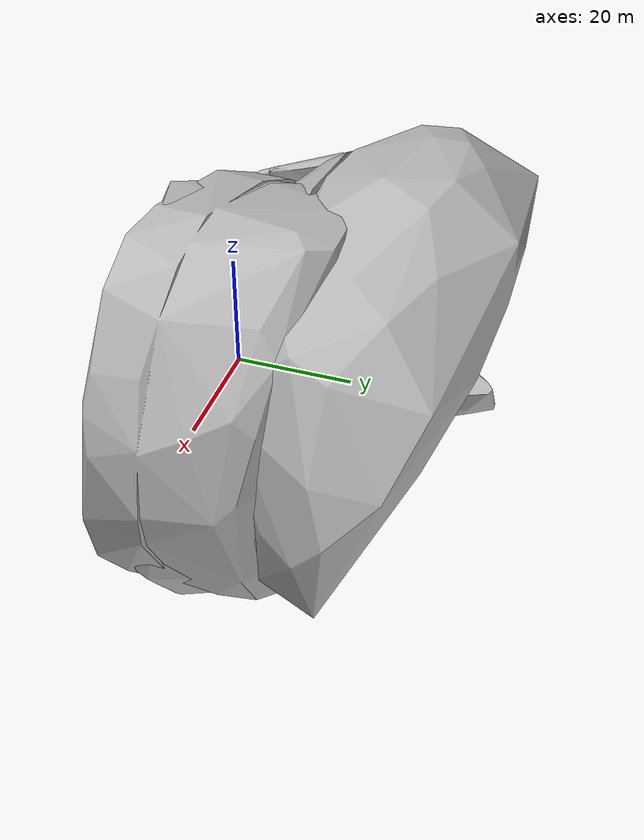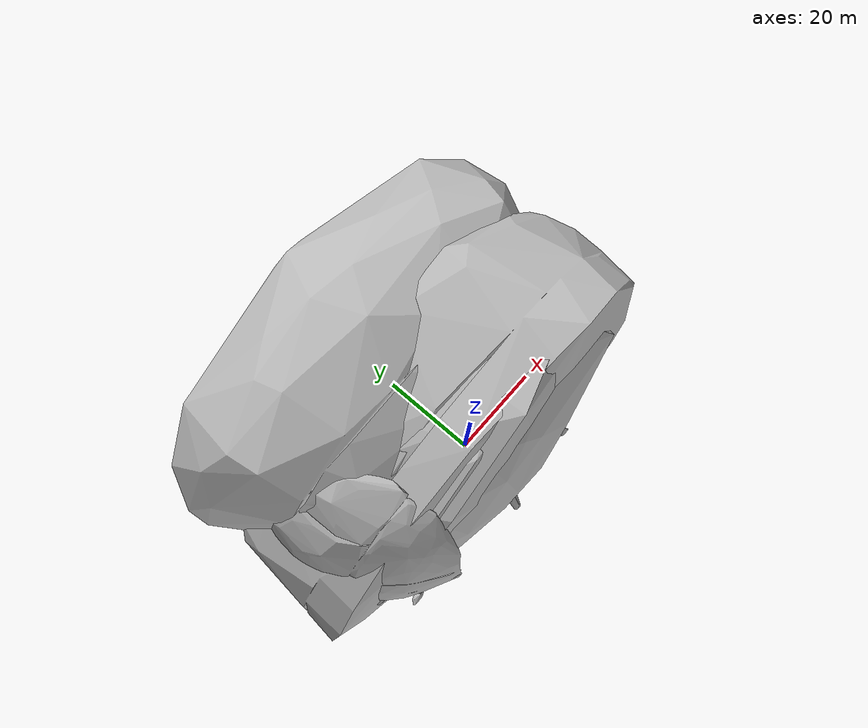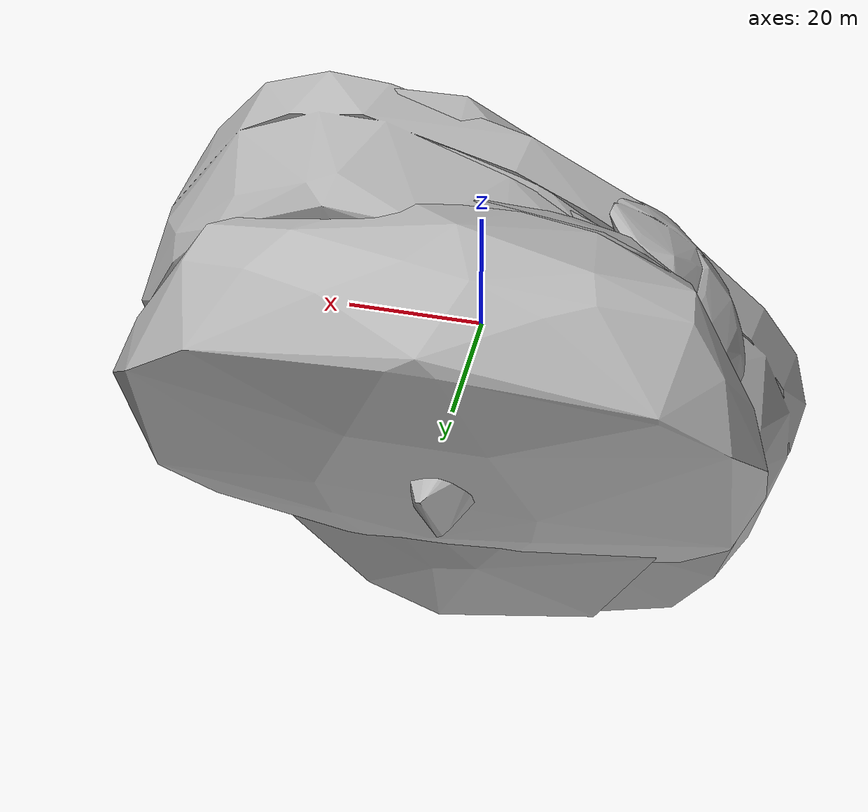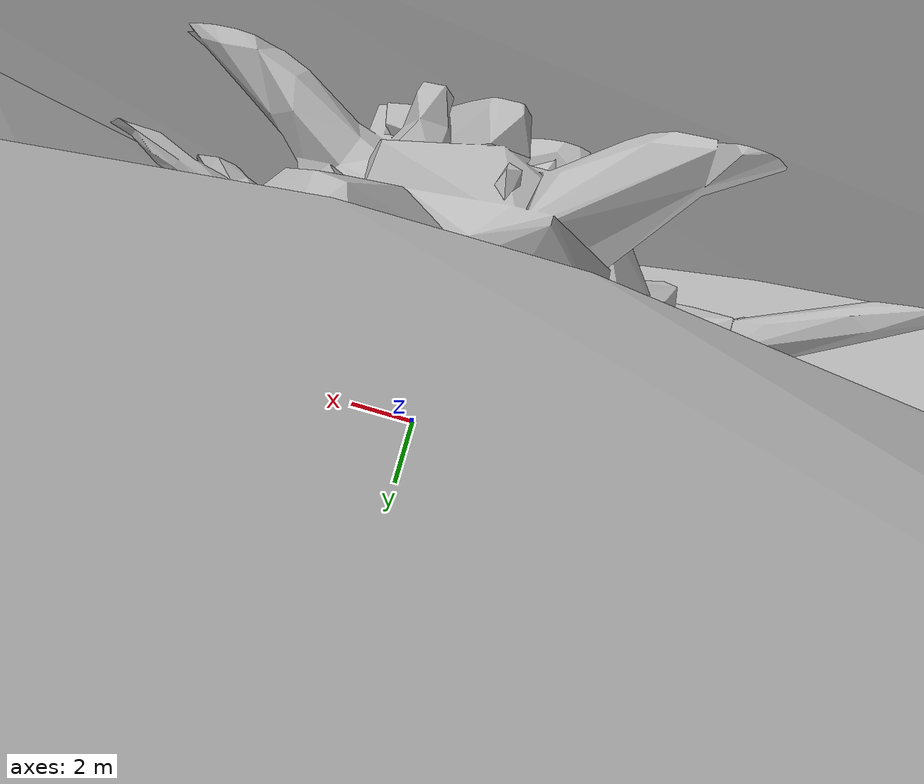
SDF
<?xml version="1.0" ?>
<sdf version="1.6">
  <world name="world">
    <model name="neuromechfly_noLimits">
      <pose>0.0 0.0 0.0 0.0 -0.0 0.0</pose>
      <link name="A1A2">
        <pose>-0.3096564710140228 -6.095955882301496e-07 0.9105792045593262 0.0 -0.0 0.0</pose>
        <inertial>
          <pose>-0.2144249677658081 -6.603514339076355e-05 0.07071342319250107 -1.5717846155166626 -2.825172185897827 -0.0002656404103618115</pose>
          <mass>8.571491383277525e-05</mass>
          <inertia>
            <ixx>5.379007258257524e-06</ixx>
            <ixy>-2.7172143083138003e-10</ixy>
            <ixz>-4.016699799635996e-07</ixz>
            <iyy>2.8840520398898414e-06</iyy>
            <iyz>1.2978086881476767e-09</iyz>
            <izz>4.283754254534721e-06</izz>
          </inertia>
        </inertial>
        <visual name="A1A2_visual">
          <pose>-2.3841858265427618e-08 -4.547473576627277e-14 -9.536743306171047e-08 0.0 -0.0 0.0</pose>
          <geometry>
            <mesh>
              <uri>../meshes/stl/A1A2.stl</uri>
              <scale>1000.0 1000.0 1000.0</scale>
            </mesh>
          </geometry>
          <material/>
        </visual>
      </link>
      <link name="A3">
        <pose>-0.666130006313324 -6.225838546924933e-07 0.9098724126815796 0.0 -0.2617993950843811 0.0</pose>
        <inertial>
          <pose>-0.05987601354718208 -6.470004882430658e-05 -0.02268083207309246 -1.570969581604004 -3.0543622970581055 -2.9826280297129415e-05</pose>
          <mass>0.00010704018580061077</mass>
          <inertia>
            <ixx>8.996426496899934e-06</ixx>
            <ixy>-1.0189078085903943e-10</ixy>
            <ixz>-2.182086660608849e-07</ixz>
            <iyy>4.18077287566254e-06</iyy>
            <iyz>4.0700063622846777e-10</iyz>
            <izz>6.520348442338967e-06</izz>
          </inertia>
        </inertial>
        <visual name="A3_visual">
          <pose>9.536743306171047e-08 -4.547473576627277e-14 -1.1920928955078125e-07 0.0 4.882812731921149e-08 0.0</pose>
          <geometry>
            <mesh>
              <uri>../meshes/stl/A3.stl</uri>
              <scale>1000.0 1000.0 1000.0</scale>
            </mesh>
          </geometry>
          <material/>
        </visual>
      </link>
      <link name="A4">
        <pose>-0.8957121968269348 -6.236073204490822e-07 0.8487271070480347 0.0 -0.5235987901687622 0.0</pose>
        <inertial>
          <pose>-0.06720209121704102 -2.9355971491895616e-05 -0.017197847366333008 -1.570814847946167 -3.0537703037261963 -5.073751162854023e-05</pose>
          <mass>9.752435108452857e-05</mass>
          <inertia>
            <ixx>8.05161514355576e-06</ixx>
            <ixy>-2.350168474990703e-10</ixy>
            <ixz>-1.6058848411617763e-07</ixz>
            <iyy>3.257527734203393e-06</iyy>
            <iyz>6.270709172547439e-11</iyz>
            <izz>6.2418857754968594e-06</izz>
          </inertia>
        </inertial>
        <visual name="A4_visual">
          <pose>0.0 0.0 0.0 0.0 -0.0 0.0</pose>
          <geometry>
            <mesh>
              <uri>../meshes/stl/A4.stl</uri>
              <scale>1000.0 1000.0 1000.0</scale>
            </mesh>
          </geometry>
          <material/>
        </visual>
      </link>
      <link name="A5">
        <pose>-1.0812511444091797 -6.25780387508712e-07 0.7414974570274353 0.0 -0.7853980660438538 0.0</pose>
        <inertial>
          <pose>-0.08348398655653 2.2320235075312667e-05 -0.040628910064697266 1.5714948177337646 3.1243011951446533 -0.0002104316372424364</pose>
          <mass>9.704450609731538e-05</mass>
          <inertia>
            <ixx>6.510006856983616e-06</ixx>
            <ixy>-6.353942720115236e-10</ixy>
            <ixz>2.510708473554063e-08</ixz>
            <iyy>3.3950607369438554e-06</iyy>
            <iyz>-1.1669246567412128e-09</iyz>
            <izz>5.0585773842176395e-06</izz>
          </inertia>
        </inertial>
        <visual name="A5_visual">
          <pose>9.536743306171047e-08 -4.547473576627277e-14 4.7683716530855236e-08 0.0 4.882812731921149e-08 0.0</pose>
          <geometry>
            <mesh>
              <uri>../meshes/stl/A5.stl</uri>
              <scale>1000.0 1000.0 1000.0</scale>
            </mesh>
          </geometry>
          <material/>
        </visual>
      </link>
      <link name="A6">
        <pose>-1.271146535873413 -6.225404263204837e-07 0.5523146390914917 0.0 -1.0471974611282349 0.0</pose>
        <inertial>
          <pose>-0.05385642126202583 1.0378301340097096e-05 -0.0347994826734066 1.5700453519821167 -3.0486338138580322 0.00011962816643062979</pose>
          <mass>6.267604318477003e-05</mass>
          <inertia>
            <ixx>2.5686907519812623e-06</ixx>
            <ixy>7.637514399896898e-11</ixy>
            <ixz>-4.9756936064053624e-08</ixz>
            <iyy>1.97061699442684e-06</iyy>
            <iyz>4.215461293405398e-11</iyz>
            <izz>2.0396207514768214e-06</izz>
          </inertia>
        </inertial>
        <visual name="A6_visual">
          <pose>0.0 -9.094947153254554e-14 0.0 0.0 -0.0 0.0</pose>
          <geometry>
            <mesh>
              <uri>../meshes/stl/A6.stl</uri>
              <scale>1000.0 1000.0 1000.0</scale>
            </mesh>
          </geometry>
          <material/>
        </visual>
      </link>
      <link name="Haustellum">
        <pose>0.5039694905281067 0.0002346131223021075 0.9939287304878235 0.0 0.698131799697876 0.0</pose>
        <inertial>
          <pose>0.20060499012470245 0.004706569481641054 -0.00878372322767973 -0.014601891860365868 -0.00142684206366539 3.123378038406372</pose>
          <mass>6.941066853014398e-06</mass>
          <inertia>
            <ixx>4.907255111440599e-08</ixx>
            <ixy>1.7929555828165396e-10</ixy>
            <ixz>4.998376081429952e-11</ixz>
            <iyy>5.8887346186315783e-08</iyy>
            <iyz>3.09533767001756e-10</iyz>
            <izz>8.014157063555477e-08</izz>
          </inertia>
        </inertial>
        <collision name="Haustellum_collision">
          <pose>7.152558367806705e-08 2.3283064712331658e-11 2.3841861818141297e-08 0.0 -0.0 0.0</pose>
          <geometry>
            <mesh>
              <uri>../meshes/stl/Haustellum.stl</uri>
              <scale>1000.0 1000.0 1000.0</scale>
            </mesh>
          </geometry>
        </collision>
        <visual name="Haustellum_visual">
          <pose>7.152558367806705e-08 2.3283064712331658e-11 2.3841861818141297e-08 0.0 -0.0 0.0</pose>
          <geometry>
            <mesh>
              <uri>../meshes/stl/Haustellum.stl</uri>
              <scale>1000.0 1000.0 1000.0</scale>
            </mesh>
          </geometry>
          <material/>
        </visual>
      </link>
      <link name="Head">
        <pose>0.49792253971099854 -6.537505328196858e-07 1.2107712030410767 0.0 0.1745329350233078 0.0</pose>
        <inertial>
          <pose>0.20209117233753204 -0.0043840003199875355 0.043947745114564896 1.4678962230682373 0.15526531636714935 0.05778481438755989</pose>
          <mass>8.113157308044636e-05</mass>
          <inertia>
            <ixx>3.916686083637349e-06</ixx>
            <ixy>5.496640594677064e-08</ixy>
            <ixz>-1.355155214169488e-07</ixz>
            <iyy>2.937974490210881e-06</iyy>
            <iyz>-1.954467052189715e-08</iyz>
            <izz>3.069572001355821e-06</izz>
          </inertia>
        </inertial>
        <collision name="Head_collision">
          <pose>-9.536743306171047e-08 -1.364242106869501e-13 -2.3841858265427618e-08 0.0 -1.2207031829802872e-08 0.0</pose>
          <geometry>
            <mesh>
              <uri>../meshes/stl/Head.stl</uri>
              <scale>1000.0 1000.0 1000.0</scale>
            </mesh>
          </geometry>
        </collision>
        <visual name="Head_visual">
          <pose>-9.536743306171047e-08 -1.364242106869501e-13 -2.3841858265427618e-08 0.0 -1.2207031829802872e-08 0.0</pose>
          <geometry>
            <mesh>
              <uri>../meshes/stl/Head.stl</uri>
              <scale>1000.0 1000.0 1000.0</scale>
            </mesh>
          </geometry>
          <material/>
        </visual>
      </link>
      <link name="Head_roll">
        <pose>0.4979226887226105 -6.537503054460103e-07 1.2107712030410767 0.0 -0.0 0.0</pose>
        <inertial>
          <pose>-4.7683716530855236e-08 -4.547473576627277e-14 -9.536743306171047e-08 -0.0 -0.0 0.0</pose>
          <mass>0.0</mass>
          <inertia>
            <ixx>0.0</ixx>
            <ixy>0.0</ixy>
            <ixz>0.0</ixz>
            <iyy>0.0</iyy>
            <iyz>0.0</iyz>
            <izz>0.0</izz>
          </inertia>
        </inertial>
      </link>
      <link name="Head_yaw">
        <pose>0.4979226291179657 -6.53750419132848e-07 1.2107712030410767 0.0 -0.0 0.0</pose>
        <inertial>
          <pose>0.0 -9.094947153254554e-14 -9.536743306171047e-08 -0.0 -0.0 0.0</pose>
          <mass>0.0</mass>
          <inertia>
            <ixx>0.0</ixx>
            <ixy>0.0</ixy>
            <ixz>0.0</ixz>
            <iyy>0.0</iyy>
            <iyz>0.0</iyz>
            <izz>0.0</izz>
          </inertia>
        </inertial>
      </link>
      <link name="LAntenna">
        <pose>0.9482773542404175 0.06690005213022232 1.2730263471603394 0.0 0.1745329350233078 0.0</pose>
        <inertial>
          <pose>0.05091390758752823 0.013138825073838234 -0.11156077682971954 1.5705833435058594 -1.4220705032348633 0.32746294140815735</pose>
          <mass>1.7777389383760332e-06</mass>
          <inertia>
            <ixx>1.2132654283335043e-08</ixx>
            <ixy>6.34643864390147e-10</ixy>
            <ixz>-1.0707396219956799e-09</ixz>
            <iyy>1.0481508781908762e-08</iyy>
            <iyz>-3.6379731017516985e-10</iyz>
            <izz>4.970367756570775e-09</izz>
          </inertia>
        </inertial>
        <collision name="LAntenna_collision">
          <pose>-9.536743306171047e-08 1.1920929132713809e-08 -1.0728836485895954e-07 0.0 -1.2207031829802872e-08 0.0</pose>
          <geometry>
            <mesh>
              <uri>../meshes/stl/LAntenna.stl</uri>
              <scale>1000.0 1000.0 1000.0</scale>
            </mesh>
          </geometry>
        </collision>
        <visual name="LAntenna_visual">
          <pose>-9.536743306171047e-08 1.1920929132713809e-08 -1.0728836485895954e-07 0.0 -1.2207031829802872e-08 0.0</pose>
          <geometry>
            <mesh>
              <uri>../meshes/stl/LAntenna.stl</uri>
              <scale>1000.0 1000.0 1000.0</scale>
            </mesh>
          </geometry>
          <material/>
        </visual>
      </link>
      <link name="LEye">
        <pose>0.7419559359550476 -5.636523496832524e-07 1.258327603340149 0.0 0.1745329350233078 0.0</pose>
        <inertial>
          <pose>-0.00703806895762682 0.3009641766548157 -0.02373889647424221 0.1506287008523941 0.08522720634937286 -1.1666679382324219</pose>
          <mass>9.502325241495403e-06</mass>
          <inertia>
            <ixx>1.3114464866873867e-07</ixx>
            <ixy>-2.390665136022388e-08</ixy>
            <ixz>-8.179075815846679e-09</ixz>
            <iyy>1.7805336805296216e-07</iyy>
            <iyz>5.857114763037776e-09</iyz>
            <izz>8.81424038962953e-08</izz>
          </inertia>
        </inertial>
        <collision name="LEye_collision">
          <pose>-4.7683716530855236e-08 -4.547473576627277e-14 -1.1920929132713809e-08 0.0 -1.2207031829802872e-08 0.0</pose>
          <geometry>
            <mesh>
              <uri>../meshes/stl/LEye.stl</uri>
              <scale>1000.0 1000.0 1000.0</scale>
            </mesh>
          </geometry>
        </collision>
        <visual name="LEye_visual">
          <pose>-4.7683716530855236e-08 -4.547473576627277e-14 -1.1920929132713809e-08 0.0 -1.2207031829802872e-08 0.0</pose>
          <geometry>
            <mesh>
              <uri>../meshes/stl/LEye.stl</uri>
              <scale>1000.0 1000.0 1000.0</scale>
            </mesh>
          </geometry>
          <material/>
        </visual>
      </link>
      <link name="LFCoxa">
        <pose>0.41799989342689514 0.2699994444847107 1.0799976587295532 0.0 -0.0 0.0</pose>
        <inertial>
          <pose>0.002981090685352683 -0.03152108192443848 -0.2531244456768036 -0.04575826972723007 -0.04927659407258034 0.5402535200119019</pose>
          <mass>5.741707610995013e-06</mass>
          <inertia>
            <ixx>5.983418637183175e-08</ixx>
            <ixy>1.5355095860900972e-09</ixy>
            <ixz>9.568855434245275e-10</ixz>
            <iyy>5.79745744876736e-08</iyy>
            <iyz>2.8728611156529988e-09</iyz>
            <izz>1.4207714613335929e-08</izz>
          </inertia>
        </inertial>
        <collision name="LFCoxa_collision">
          <pose>4.7683716530855236e-08 2.3841858265427618e-08 0.0 0.0 -0.0 0.0</pose>
          <geometry>
            <mesh>
              <uri>../meshes/stl/LFCoxa.stl</uri>
              <scale>1000.0 1000.0 1000.0</scale>
            </mesh>
          </geometry>
        </collision>
        <visual name="LFCoxa_visual">
          <pose>4.7683716530855236e-08 2.3841858265427618e-08 0.0 0.0 -0.0 0.0</pose>
          <geometry>
            <mesh>
              <uri>../meshes/stl/LFCoxa.stl</uri>
              <scale>1000.0 1000.0 1000.0</scale>
            </mesh>
          </geometry>
          <material/>
        </visual>
      </link>
      <link name="LFCoxa_roll">
        <pose>0.41799989342689514 0.2699994444847107 1.0799976587295532 0.0 -0.0 0.0</pose>
        <inertial>
          <pose>4.7683716530855236e-08 2.3841858265427618e-08 0.0 -0.0 -0.0 0.0</pose>
          <mass>0.0</mass>
          <inertia>
            <ixx>0.0</ixx>
            <ixy>0.0</ixy>
            <ixz>0.0</ixz>
            <iyy>0.0</iyy>
            <iyz>0.0</iyz>
            <izz>0.0</izz>
          </inertia>
        </inertial>
      </link>
      <link name="LFCoxa_yaw">
        <pose>0.41799989342689514 0.2699994444847107 1.0799976587295532 0.0 -0.0 0.0</pose>
        <inertial>
          <pose>4.7683716530855236e-08 2.3841858265427618e-08 0.0 -0.0 -0.0 0.0</pose>
          <mass>0.0</mass>
          <inertia>
            <ixx>0.0</ixx>
            <ixy>0.0</ixy>
            <ixz>0.0</ixz>
            <iyy>0.0</iyy>
            <iyz>0.0</iyz>
            <izz>0.0</izz>
          </inertia>
        </inertial>
      </link>
      <link name="LFFemur">
        <pose>0.41799989342689514 0.2699994444847107 0.6545163989067078 0.0 -0.0 0.0</pose>
        <inertial>
          <pose>-0.01985769346356392 -0.006747388746589422 -0.35944435000419617 0.05809097737073898 1.6430429220199585 1.0958921909332275</pose>
          <mass>7.992114412322805e-06</mass>
          <inertia>
            <ixx>2.7267902127637655e-07</ixx>
            <ixy>2.2529365411735334e-10</ixy>
            <ixz>-8.562267397467378e-09</ixz>
            <iyy>2.732996498121526e-07</iyy>
            <iyz>-1.6672479243976315e-08</iyz>
            <izz>1.5735837661850214e-08</izz>
          </inertia>
        </inertial>
        <collision name="LFFemur_collision">
          <pose>4.7683716530855236e-08 2.3841858265427618e-08 0.0 0.0 -0.0 0.0</pose>
          <geometry>
            <mesh>
              <uri>../meshes/stl/LFFemur.stl</uri>
              <scale>1000.0 1000.0 1000.0</scale>
            </mesh>
          </geometry>
        </collision>
        <visual name="LFFemur_visual">
          <pose>4.7683716530855236e-08 2.3841858265427618e-08 0.0 0.0 -0.0 0.0</pose>
          <geometry>
            <mesh>
              <uri>../meshes/stl/LFFemur.stl</uri>
              <scale>1000.0 1000.0 1000.0</scale>
            </mesh>
          </geometry>
          <material/>
        </visual>
      </link>
      <link name="LFFemur_roll">
        <pose>0.41799989342689514 0.2699994444847107 0.6545163989067078 0.0 -0.0 0.0</pose>
        <inertial>
          <pose>4.7683716530855236e-08 2.3841858265427618e-08 0.0 -0.0 -0.0 0.0</pose>
          <mass>0.0</mass>
          <inertia>
            <ixx>0.0</ixx>
            <ixy>0.0</ixy>
            <ixz>0.0</ixz>
            <iyy>0.0</iyy>
            <iyz>0.0</iyz>
            <izz>0.0</izz>
          </inertia>
        </inertial>
      </link>
      <link name="LFTarsus1">
        <pose>0.41799989342689514 0.2699994444847107 -0.5691056251525879 0.0 -0.0 0.0</pose>
        <inertial>
          <pose>-0.004590225405991077 -0.009428716264665127 -0.12341504544019699 -2.4325931072235107 -1.5347644090652466 -0.27972275018692017</pose>
          <mass>5.902334137063546e-07</mass>
          <inertia>
            <ixx>2.6619196564244832e-09</ixx>
            <ixy>-6.696196350980393e-12</ixy>
            <ixz>-8.499819284680847e-11</ixz>
            <iyy>2.671119021702012e-09</iyy>
            <iyz>2.4720518054378474e-11</iyz>
            <izz>2.137105482392998e-10</izz>
          </inertia>
        </inertial>
        <collision name="LFTarsus1_collision">
          <pose>4.7683716530855236e-08 2.3841858265427618e-08 0.0 0.0 -0.0 0.0</pose>
          <geometry>
            <mesh>
              <uri>../meshes/stl/LFTarsus1.stl</uri>
              <scale>1000.0 1000.0 1000.0</scale>
            </mesh>
          </geometry>
        </collision>
        <visual name="LFTarsus1_visual">
          <pose>4.7683716530855236e-08 2.3841858265427618e-08 0.0 0.0 -0.0 0.0</pose>
          <geometry>
            <mesh>
              <uri>../meshes/stl/LFTarsus1.stl</uri>
              <scale>1000.0 1000.0 1000.0</scale>
            </mesh>
          </geometry>
          <material/>
        </visual>
      </link>
      <link name="LFTarsus2">
        <pose>0.41799989342689514 0.2699994444847107 -0.7946224808692932 0.0 -0.0 0.0</pose>
        <inertial>
          <pose>-0.0012888432247564197 -0.005322647280991077 -0.08914299309253693 0.7475926280021667 1.5205031633377075 0.06141802296042442</pose>
          <mass>2.658976343874435e-07</mass>
          <inertia>
            <ixx>5.103329322322616e-10</ixx>
            <ixy>-4.652931733921339e-12</ixy>
            <ixz>2.2319235150477887e-11</ixz>
            <iyy>5.110168665053002e-10</iyy>
            <iyz>1.141795723786161e-12</iyz>
            <izz>6.692566660715184e-11</izz>
          </inertia>
        </inertial>
        <collision name="LFTarsus2_collision">
          <pose>4.7683716530855236e-08 2.3841858265427618e-08 9.536743306171047e-08 0.0 -0.0 0.0</pose>
          <geometry>
            <mesh>
              <uri>../meshes/stl/LFTarsus2.stl</uri>
              <scale>1000.0 1000.0 1000.0</scale>
            </mesh>
          </geometry>
        </collision>
        <visual name="LFTarsus2_visual">
          <pose>4.7683716530855236e-08 2.3841858265427618e-08 9.536743306171047e-08 0.0 -0.0 0.0</pose>
          <geometry>
            <mesh>
              <uri>../meshes/stl/LFTarsus2.stl</uri>
              <scale>1000.0 1000.0 1000.0</scale>
            </mesh>
          </geometry>
          <material/>
        </visual>
      </link>
      <link name="LFTarsus3">
        <pose>0.41799989342689514 0.2699994444847107 -0.9482911229133606 0.0 -0.0 0.0</pose>
        <inertial>
          <pose>-0.0010801792377606034 -0.003454184625297785 -0.05935249477624893 1.238088846206665 1.4883233308792114 -0.43491798639297485</pose>
          <mass>1.5048445915428457e-07</mass>
          <inertia>
            <ixx>1.2943798832106454e-10</ixx>
            <ixy>-1.636254884174268e-12</ixy>
            <ixz>7.384017845364119e-12</ixz>
            <iyy>1.2973339477855396e-10</iyy>
            <iyz>-3.5369691091179722e-12</iyz>
            <izz>3.237591364465404e-11</izz>
          </inertia>
        </inertial>
        <collision name="LFTarsus3_collision">
          <pose>4.7683716530855236e-08 2.3841858265427618e-08 0.0 0.0 -0.0 0.0</pose>
          <geometry>
            <mesh>
              <uri>../meshes/stl/LFTarsus3.stl</uri>
              <scale>1000.0 1000.0 1000.0</scale>
            </mesh>
          </geometry>
        </collision>
        <visual name="LFTarsus3_visual">
          <pose>4.7683716530855236e-08 2.3841858265427618e-08 0.0 0.0 -0.0 0.0</pose>
          <geometry>
            <mesh>
              <uri>../meshes/stl/LFTarsus3.stl</uri>
              <scale>1000.0 1000.0 1000.0</scale>
            </mesh>
          </geometry>
          <material/>
        </visual>
      </link>
      <link name="LFTarsus4">
        <pose>0.41799989342689514 0.2699994444847107 -1.0467886924743652 0.0 -0.0 0.0</pose>
        <inertial>
          <pose>0.0008697509765625 -0.0014729738468304276 -0.0499730110168457 2.7276172637939453 1.4870373010635376 -0.4084789454936981</pose>
          <mass>1.1769954786975934e-07</mass>
          <inertia>
            <ixx>7.574844946658414e-11</ixx>
            <ixy>-1.1218003527775303e-12</ixy>
            <ixz>4.142658799359131e-12</ixz>
            <iyy>7.619289827697055e-11</iyy>
            <iyz>-1.8782525110208446e-12</iyz>
            <izz>2.2848746233067172e-11</izz>
          </inertia>
        </inertial>
        <collision name="LFTarsus4_collision">
          <pose>4.7683716530855236e-08 2.3841858265427618e-08 -9.536743306171047e-08 0.0 -0.0 0.0</pose>
          <geometry>
            <mesh>
              <uri>../meshes/stl/LFTarsus4.stl</uri>
              <scale>1000.0 1000.0 1000.0</scale>
            </mesh>
          </geometry>
        </collision>
        <visual name="LFTarsus4_visual">
          <pose>4.7683716530855236e-08 2.3841858265427618e-08 -9.536743306171047e-08 0.0 -0.0 0.0</pose>
          <geometry>
            <mesh>
              <uri>../meshes/stl/LFTarsus4.stl</uri>
              <scale>1000.0 1000.0 1000.0</scale>
            </mesh>
          </geometry>
          <material/>
        </visual>
      </link>
      <link name="LFTarsus5">
        <pose>0.41799989342689514 0.2699994444847107 -1.1337875127792358 0.0 -0.0 0.0</pose>
        <inertial>
          <pose>0.0025776387192308903 -0.0008883714908733964 -0.05205802991986275 1.3573890924453735 -1.6784626245498657 -0.10700388252735138</pose>
          <mass>1.4544444513923852e-07</mass>
          <inertia>
            <ixx>1.135124894575874e-10</ixx>
            <ixy>-5.371669362193046e-13</ixy>
            <ixz>8.61959329236233e-12</ixz>
            <iyy>1.203871149303067e-10</iyy>
            <iyz>-1.0622825672702412e-12</iyz>
            <izz>3.4301165518026506e-11</izz>
          </inertia>
        </inertial>
        <collision name="LFTarsus5_collision">
          <pose>4.7683716530855236e-08 2.3841858265427618e-08 0.0 0.0 -0.0 0.0</pose>
          <geometry>
            <mesh>
              <uri>../meshes/stl/LFTarsus5.stl</uri>
              <scale>1000.0 1000.0 1000.0</scale>
            </mesh>
          </geometry>
        </collision>
        <visual name="LFTarsus5_visual">
          <pose>4.7683716530855236e-08 2.3841858265427618e-08 0.0 0.0 -0.0 0.0</pose>
          <geometry>
            <mesh>
              <uri>../meshes/stl/LFTarsus5.stl</uri>
              <scale>1000.0 1000.0 1000.0</scale>
            </mesh>
          </geometry>
          <material/>
        </visual>
      </link>
      <link name="LFTibia">
        <pose>0.41799989342689514 0.2699994444847107 -0.05072354897856712 0.0 -0.0 0.0</pose>
        <inertial>
          <pose>0.011397170834243298 -0.0035875558387488127 -0.2930237948894501 0.11941991001367569 1.6242852210998535 -2.2962098121643066</pose>
          <mass>2.6268343212263377e-06</mass>
          <inertia>
            <ixx>5.50390271997034e-08</ixx>
            <ixy>1.5267819432842367e-10</ixy>
            <ixz>1.8890251848431905e-09</ixz>
            <iyy>5.5191946361538317e-08</iyy>
            <iyz>2.1350840278172453e-09</iyz>
            <izz>2.18284819569887e-09</izz>
          </inertia>
        </inertial>
        <collision name="LFTibia_collision">
          <pose>4.7683716530855236e-08 2.3841858265427618e-08 0.0 0.0 -0.0 0.0</pose>
          <geometry>
            <mesh>
              <uri>../meshes/stl/LFTibia.stl</uri>
              <scale>1000.0 1000.0 1000.0</scale>
            </mesh>
          </geometry>
        </collision>
        <visual name="LFTibia_visual">
          <pose>4.7683716530855236e-08 2.3841858265427618e-08 0.0 0.0 -0.0 0.0</pose>
          <geometry>
            <mesh>
              <uri>../meshes/stl/LFTibia.stl</uri>
              <scale>1000.0 1000.0 1000.0</scale>
            </mesh>
          </geometry>
          <material/>
        </visual>
      </link>
      <link name="LHaltere">
        <pose>-0.2589678168296814 0.21355578303337097 0.9370104670524597 0.0 -0.0 0.0</pose>
        <inertial>
          <pose>-0.008205438032746315 0.2060527801513672 -0.0006526947254315019 -1.5760596990585327 0.0750126913189888 -0.001004880527034402</pose>
          <mass>1.4160896935430824e-06</mass>
          <inertia>
            <ixx>1.4020303628986903e-08</ixx>
            <ixy>-1.6711254076134715e-11</ixy>
            <ixz>-2.8079219660502452e-11</ixz>
            <iyy>1.9730319364747313e-09</iyy>
            <iyz>-6.1248840665395e-11</iyz>
            <izz>1.3649625794138886e-08</izz>
          </inertia>
        </inertial>
        <visual name="LHaltere_visual">
          <pose>-2.3841858265427618e-08 2.3841858265427618e-08 0.0 0.0 -0.0 0.0</pose>
          <geometry>
            <mesh>
              <uri>../meshes/stl/LHaltere.stl</uri>
              <scale>1000.0 1000.0 1000.0</scale>
            </mesh>
          </geometry>
          <material/>
        </visual>
      </link>
      <link name="LHaltere_roll">
        <pose>-0.2589678168296814 0.2135557234287262 0.9370104670524597 0.0 -0.0 0.0</pose>
        <inertial>
          <pose>-2.3841858265427618e-08 2.3841858265427618e-08 0.0 -0.0 -0.0 0.0</pose>
          <mass>0.0</mass>
          <inertia>
            <ixx>0.0</ixx>
            <ixy>0.0</ixy>
            <ixz>0.0</ixz>
            <iyy>0.0</iyy>
            <iyz>0.0</iyz>
            <izz>0.0</izz>
          </inertia>
        </inertial>
      </link>
      <link name="LHaltere_yaw">
        <pose>-0.2589678168296814 0.21355575323104858 0.9370104670524597 0.0 -0.0 0.0</pose>
        <inertial>
          <pose>-2.3841858265427618e-08 2.3841858265427618e-08 0.0 -0.0 -0.0 0.0</pose>
          <mass>0.0</mass>
          <inertia>
            <ixx>0.0</ixx>
            <ixy>0.0</ixy>
            <ixz>0.0</ixz>
            <iyy>0.0</iyy>
            <iyz>0.0</iyz>
            <izz>0.0</izz>
          </inertia>
        </inertial>
      </link>
      <link name="LHCoxa">
        <pose>-0.14771771430969238 0.08699285238981247 0.6072233319282532 0.0 -0.0 0.0</pose>
        <inertial>
          <pose>-0.00381984724663198 0.02095385268330574 -0.10100875049829483 -0.1921551674604416 -1.2247354984283447 -1.7353719472885132</pose>
          <mass>3.2548936150106453e-06</mass>
          <inertia>
            <ixx>1.350804012338567e-08</ixx>
            <ixy>-1.6370509791399278e-10</ixy>
            <ixz>2.639987688459687e-10</ixz>
            <iyy>1.4484483552670528e-08</iyy>
            <iyz>2.2778771682240345e-09</iyz>
            <izz>8.879176902911457e-09</izz>
          </inertia>
        </inertial>
        <collision name="LHCoxa_collision">
          <pose>-1.1920929132713809e-08 0.0 -4.7683716530855236e-08 0.0 -0.0 0.0</pose>
          <geometry>
            <mesh>
              <uri>../meshes/stl/LHCoxa.stl</uri>
              <scale>1000.0 1000.0 1000.0</scale>
            </mesh>
          </geometry>
        </collision>
        <visual name="LHCoxa_visual">
          <pose>-1.1920929132713809e-08 0.0 -4.7683716530855236e-08 0.0 -0.0 0.0</pose>
          <geometry>
            <mesh>
              <uri>../meshes/stl/LHCoxa.stl</uri>
              <scale>1000.0 1000.0 1000.0</scale>
            </mesh>
          </geometry>
          <material/>
        </visual>
      </link>
      <link name="LHCoxa_roll">
        <pose>-0.14771771430969238 0.08699285238981247 0.6072233319282532 0.0 -0.0 0.0</pose>
        <inertial>
          <pose>-1.1920929132713809e-08 0.0 -4.7683716530855236e-08 -0.0 -0.0 0.0</pose>
          <mass>0.0</mass>
          <inertia>
            <ixx>0.0</ixx>
            <ixy>0.0</ixy>
            <ixz>0.0</ixz>
            <iyy>0.0</iyy>
            <iyz>0.0</iyz>
            <izz>0.0</izz>
          </inertia>
        </inertial>
      </link>
      <link name="LHCoxa_yaw">
        <pose>-0.14771771430969238 0.08699285238981247 0.6072233319282532 0.0 -0.0 0.0</pose>
        <inertial>
          <pose>-1.1920929132713809e-08 0.0 -4.7683716530855236e-08 -0.0 -0.0 0.0</pose>
          <mass>0.0</mass>
          <inertia>
            <ixx>0.0</ixx>
            <ixy>0.0</ixy>
            <ixz>0.0</ixz>
            <iyy>0.0</iyy>
            <iyz>0.0</iyz>
            <izz>0.0</izz>
          </inertia>
        </inertial>
      </link>
      <link name="LHFemur">
        <pose>-0.14799241721630096 0.0867670401930809 0.40780624747276306 0.0 -0.0 0.0</pose>
        <inertial>
          <pose>0.03316854313015938 -0.018455756828188896 -0.43907615542411804 -0.09183122962713242 1.5981299877166748 -2.257822036743164</pose>
          <mass>1.1113719808091789e-05</mass>
          <inertia>
            <ixx>5.240769260201016e-07</ixx>
            <ixy>3.451887877192935e-09</ixy>
            <ixz>8.697293494739268e-09</ixz>
            <iyy>5.240994330025576e-07</iyy>
            <iyz>1.0573373286421583e-08</iyz>
            <izz>2.7097994814382908e-08</izz>
          </inertia>
        </inertial>
        <collision name="LHFemur_collision">
          <pose>-1.1920929132713809e-08 5.9604645663569045e-09 0.0 0.0 -0.0 0.0</pose>
          <geometry>
            <mesh>
              <uri>../meshes/stl/LHFemur.stl</uri>
              <scale>1000.0 1000.0 1000.0</scale>
            </mesh>
          </geometry>
        </collision>
        <visual name="LHFemur_visual">
          <pose>-1.1920929132713809e-08 5.9604645663569045e-09 0.0 0.0 -0.0 0.0</pose>
          <geometry>
            <mesh>
              <uri>../meshes/stl/LHFemur.stl</uri>
              <scale>1000.0 1000.0 1000.0</scale>
            </mesh>
          </geometry>
          <material/>
        </visual>
      </link>
      <link name="LHFemur_roll">
        <pose>-0.14799241721630096 0.0867670401930809 0.40780624747276306 0.0 -0.0 0.0</pose>
        <inertial>
          <pose>-1.1920929132713809e-08 5.9604645663569045e-09 0.0 -0.0 -0.0 0.0</pose>
          <mass>0.0</mass>
          <inertia>
            <ixx>0.0</ixx>
            <ixy>0.0</ixy>
            <ixz>0.0</ixz>
            <iyy>0.0</iyy>
            <iyz>0.0</iyz>
            <izz>0.0</izz>
          </inertia>
        </inertial>
      </link>
      <link name="LHTarsus1">
        <pose>-0.1475965529680252 0.08577121049165726 -1.1129627227783203 0.0 -0.0 0.0</pose>
        <inertial>
          <pose>-0.002593171549960971 0.004060101695358753 -0.16763964295387268 -1.2112128734588623 1.5842970609664917 -0.6816954612731934</pose>
          <mass>1.3249969982172918e-06</mass>
          <inertia>
            <ixx>1.3948833895937138e-08</ixx>
            <ixy>-3.408937645724606e-11</ixy>
            <ixz>-1.3881187401653182e-10</ixz>
            <iyy>1.3855442366983524e-08</iyy>
            <iyz>1.1197135410054028e-10</iyz>
            <izz>7.38346273473165e-10</izz>
          </inertia>
        </inertial>
        <collision name="LHTarsus1_collision">
          <pose>-3.5762788286319847e-08 -1.1920929132713809e-08 0.0 0.0 -0.0 0.0</pose>
          <geometry>
            <mesh>
              <uri>../meshes/stl/LHTarsus1.stl</uri>
              <scale>1000.0 1000.0 1000.0</scale>
            </mesh>
          </geometry>
        </collision>
        <visual name="LHTarsus1_visual">
          <pose>-3.5762788286319847e-08 -1.1920929132713809e-08 0.0 0.0 -0.0 0.0</pose>
          <geometry>
            <mesh>
              <uri>../meshes/stl/LHTarsus1.stl</uri>
              <scale>1000.0 1000.0 1000.0</scale>
            </mesh>
          </geometry>
          <material/>
        </visual>
      </link>
      <link name="LHTarsus2">
        <pose>-0.14765509963035583 0.08641671389341354 -1.4657052755355835 0.0 -0.0 0.0</pose>
        <inertial>
          <pose>-0.0013342738384380937 0.002292776247486472 -0.09138822555541992 -2.0987155437469482 -1.6082539558410645 -0.9173864722251892</pose>
          <mass>4.465595046515482e-07</mass>
          <inertia>
            <ixx>1.2421568618269873e-09</ixx>
            <ixy>3.9195335774079074e-12</ixy>
            <ixz>2.460386567916838e-11</ixz>
            <iyy>1.248205629659075e-09</iyy>
            <iyz>-3.238046634512226e-11</iyz>
            <izz>1.5854710744795977e-10</izz>
          </inertia>
        </inertial>
        <collision name="LHTarsus2_collision">
          <pose>1.1920929132713809e-08 0.0 0.0 0.0 -0.0 0.0</pose>
          <geometry>
            <mesh>
              <uri>../meshes/stl/LHTarsus2.stl</uri>
              <scale>1000.0 1000.0 1000.0</scale>
            </mesh>
          </geometry>
        </collision>
        <visual name="LHTarsus2_visual">
          <pose>1.1920929132713809e-08 0.0 0.0 0.0 -0.0 0.0</pose>
          <geometry>
            <mesh>
              <uri>../meshes/stl/LHTarsus2.stl</uri>
              <scale>1000.0 1000.0 1000.0</scale>
            </mesh>
          </geometry>
          <material/>
        </visual>
      </link>
      <link name="LHTarsus3">
        <pose>-0.1476357877254486 0.08545082807540894 -1.6407579183578491 0.0 -0.0 0.0</pose>
        <inertial>
          <pose>-0.004137087147682905 0.003209739923477173 -0.04882469400763512 -0.006300854030996561 0.010789205320179462 2.7138960361480713</pose>
          <mass>1.717215492644912e-07</mass>
          <inertia>
            <ixx>1.5704891128179778e-10</ixx>
            <ixy>1.5793452052281098e-12</ixy>
            <ixz>8.109874817632491e-13</ixz>
            <iyy>1.597724065762652e-10</iyy>
            <iyz>-1.1885304928094258e-12</iyz>
            <izz>4.22558145229839e-11</izz>
          </inertia>
        </inertial>
        <collision name="LHTarsus3_collision">
          <pose>-1.1920929132713809e-08 0.0 -1.9073486612342094e-07 0.0 -0.0 0.0</pose>
          <geometry>
            <mesh>
              <uri>../meshes/stl/LHTarsus3.stl</uri>
              <scale>1000.0 1000.0 1000.0</scale>
            </mesh>
          </geometry>
        </collision>
        <visual name="LHTarsus3_visual">
          <pose>-1.1920929132713809e-08 0.0 -1.9073486612342094e-07 0.0 -0.0 0.0</pose>
          <geometry>
            <mesh>
              <uri>../meshes/stl/LHTarsus3.stl</uri>
              <scale>1000.0 1000.0 1000.0</scale>
            </mesh>
          </geometry>
          <material/>
        </visual>
      </link>
      <link name="LHTarsus4">
        <pose>-0.14762914180755615 0.0864085778594017 -1.7374663352966309 0.0 -0.0 0.0</pose>
        <inertial>
          <pose>0.0 0.0 0.0 -2.3722527027130127 -1.6625993251800537 -0.46709567308425903</pose>
          <mass>1.1443416496255567e-07</mass>
          <inertia>
            <ixx>2.4683293542298094e-10</ixx>
            <ixy>9.952485385943712e-15</ixy>
            <ixz>1.827232963853714e-11</ixz>
            <iyy>2.4985275489620366e-10</iyy>
            <iyz>-9.339634542772557e-12</iyz>
            <izz>2.642573729500649e-11</izz>
          </inertia>
        </inertial>
        <collision name="LHTarsus4_collision">
          <pose>0.0 0.0 0.0 0.0 -0.0 0.0</pose>
          <geometry>
            <mesh>
              <uri>../meshes/stl/LHTarsus4.stl</uri>
              <scale>1000.0 1000.0 1000.0</scale>
            </mesh>
          </geometry>
        </collision>
        <visual name="LHTarsus4_visual">
          <pose>0.0 0.0 0.0 0.0 -0.0 0.0</pose>
          <geometry>
            <mesh>
              <uri>../meshes/stl/LHTarsus4.stl</uri>
              <scale>1000.0 1000.0 1000.0</scale>
            </mesh>
          </geometry>
          <material/>
        </visual>
      </link>
      <link name="LHTarsus5">
        <pose>-0.147557333111763 0.08615516871213913 -1.8107707500457764 0.0 -0.0 0.0</pose>
        <inertial>
          <pose>-0.0017647624481469393 -0.0003560960467439145 -0.0526086799800396 -1.1455318927764893 -1.6402281522750854 0.28557726740837097</pose>
          <mass>1.5831647994397422e-07</mass>
          <inertia>
            <ixx>1.275534557952797e-10</ixx>
            <ixy>1.0387493793363336e-12</ixy>
            <ixz>5.673485524053406e-12</ixz>
            <iyy>1.3596468492812532e-10</iyy>
            <iyz>1.8938777007182306e-12</iyz>
            <izz>4.324883583492056e-11</izz>
          </inertia>
        </inertial>
        <collision name="LHTarsus5_collision">
          <pose>-2.3841858265427618e-08 0.0 0.0 0.0 -0.0 0.0</pose>
          <geometry>
            <mesh>
              <uri>../meshes/stl/LHTarsus5.stl</uri>
              <scale>1000.0 1000.0 1000.0</scale>
            </mesh>
          </geometry>
        </collision>
        <visual name="LHTarsus5_visual">
          <pose>-2.3841858265427618e-08 0.0 0.0 0.0 -0.0 0.0</pose>
          <geometry>
            <mesh>
              <uri>../meshes/stl/LHTarsus5.stl</uri>
              <scale>1000.0 1000.0 1000.0</scale>
            </mesh>
          </geometry>
          <material/>
        </visual>
      </link>
      <link name="LHTibia">
        <pose>-0.14785665273666382 0.08640384674072266 -0.4285075068473816 0.0 -0.0 0.0</pose>
        <inertial>
          <pose>0.023327672854065895 -0.015456504188477993 -0.4177219569683075 2.3637614250183105 1.516633152961731 -0.22312939167022705</pose>
          <mass>4.280437218327039e-06</mass>
          <inertia>
            <ixx>1.36571973333874e-07</ixx>
            <ixy>-3.589734864313778e-10</ixy>
            <ixz>6.984979984449975e-09</ixz>
            <iyy>1.373299267463762e-07</iyy>
            <iyz>-1.6120199397614828e-09</iyz>
            <izz>4.931242386774536e-09</izz>
          </inertia>
        </inertial>
        <collision name="LHTibia_collision">
          <pose>-1.1920929132713809e-08 0.0 9.536743306171047e-08 0.0 -0.0 0.0</pose>
          <geometry>
            <mesh>
              <uri>../meshes/stl/LHTibia.stl</uri>
              <scale>1000.0 1000.0 1000.0</scale>
            </mesh>
          </geometry>
        </collision>
        <visual name="LHTibia_visual">
          <pose>-1.1920929132713809e-08 0.0 9.536743306171047e-08 0.0 -0.0 0.0</pose>
          <geometry>
            <mesh>
              <uri>../meshes/stl/LHTibia.stl</uri>
              <scale>1000.0 1000.0 1000.0</scale>
            </mesh>
          </geometry>
          <material/>
        </visual>
      </link>
      <link name="LMCoxa">
        <pose>0.06767541915178299 0.1249004602432251 0.6798476576805115 0.0 -0.0 0.0</pose>
        <inertial>
          <pose>-0.001341104507446289 0.004880380816757679 -0.07880979031324387 0.03391338884830475 -1.016937494277954 -1.6626431941986084</pose>
          <mass>3.295969018637448e-06</mass>
          <inertia>
            <ixx>1.613857024264124e-08</ixx>
            <ixy>-5.2331361478733376e-11</ixy>
            <ixz>4.438624551510217e-10</ixz>
            <iyy>1.504033067194571e-08</iyy>
            <iyz>4.489648201221683e-09</iyz>
            <izz>1.0534992499367083e-08</izz>
          </inertia>
        </inertial>
        <collision name="LMCoxa_collision">
          <pose>0.0 -1.1920929132713809e-08 0.0 0.0 -0.0 0.0</pose>
          <geometry>
            <mesh>
              <uri>../meshes/stl/LMCoxa.stl</uri>
              <scale>1000.0 1000.0 1000.0</scale>
            </mesh>
          </geometry>
        </collision>
        <visual name="LMCoxa_visual">
          <pose>0.0 -1.1920929132713809e-08 0.0 0.0 -0.0 0.0</pose>
          <geometry>
            <mesh>
              <uri>../meshes/stl/LMCoxa.stl</uri>
              <scale>1000.0 1000.0 1000.0</scale>
            </mesh>
          </geometry>
          <material/>
        </visual>
      </link>
      <link name="LMCoxa_roll">
        <pose>0.06767541915178299 0.12490043044090271 0.6798476576805115 0.0 -0.0 0.0</pose>
        <inertial>
          <pose>0.0 -1.1920929132713809e-08 0.0 -0.0 -0.0 0.0</pose>
          <mass>0.0</mass>
          <inertia>
            <ixx>0.0</ixx>
            <ixy>0.0</ixy>
            <ixz>0.0</ixz>
            <iyy>0.0</iyy>
            <iyz>0.0</iyz>
            <izz>0.0</izz>
          </inertia>
        </inertial>
      </link>
      <link name="LMCoxa_yaw">
        <pose>0.06767541915178299 0.1249004453420639 0.6798476576805115 0.0 -0.0 0.0</pose>
        <inertial>
          <pose>0.0 -1.1920929132713809e-08 0.0 -0.0 -0.0 0.0</pose>
          <mass>0.0</mass>
          <inertia>
            <ixx>0.0</ixx>
            <ixy>0.0</ixy>
            <ixz>0.0</ixz>
            <iyy>0.0</iyy>
            <iyz>0.0</iyz>
            <izz>0.0</izz>
          </inertia>
        </inertial>
      </link>
      <link name="LMFemur">
        <pose>0.0674595758318901 0.12510620057582855 0.4984009861946106 0.0 -0.0 0.0</pose>
        <inertial>
          <pose>0.02351526729762554 0.002180075738579035 -0.40512463450431824 -0.819880485534668 -1.5611728429794312 -1.9618542194366455</pose>
          <mass>8.23079136553737e-06</mass>
          <inertia>
            <ixx>4.0989546919810974e-07</ixx>
            <ixy>-1.0178035657241587e-10</ixy>
            <ixz>1.4528507113592936e-09</ixz>
            <iyy>4.100231084980835e-07</iyy>
            <iyz>3.526875993502687e-09</iyz>
            <izz>1.3630461220192824e-08</izz>
          </inertia>
        </inertial>
        <collision name="LMFemur_collision">
          <pose>5.9604645663569045e-09 1.1920929132713809e-08 4.7683716530855236e-08 0.0 -0.0 0.0</pose>
          <geometry>
            <mesh>
              <uri>../meshes/stl/LMFemur.stl</uri>
              <scale>1000.0 1000.0 1000.0</scale>
            </mesh>
          </geometry>
        </collision>
        <visual name="LMFemur_visual">
          <pose>5.9604645663569045e-09 1.1920929132713809e-08 4.7683716530855236e-08 0.0 -0.0 0.0</pose>
          <geometry>
            <mesh>
              <uri>../meshes/stl/LMFemur.stl</uri>
              <scale>1000.0 1000.0 1000.0</scale>
            </mesh>
          </geometry>
          <material/>
        </visual>
      </link>
      <link name="LMFemur_roll">
        <pose>0.0674595758318901 0.12510620057582855 0.49840104579925537 0.0 -0.0 0.0</pose>
        <inertial>
          <pose>5.9604645663569045e-09 1.1920929132713809e-08 0.0 -0.0 -0.0 0.0</pose>
          <mass>0.0</mass>
          <inertia>
            <ixx>0.0</ixx>
            <ixy>0.0</ixy>
            <ixz>0.0</ixz>
            <iyy>0.0</iyy>
            <iyz>0.0</iyz>
            <izz>0.0</izz>
          </inertia>
        </inertial>
      </link>
      <link name="LMTarsus1">
        <pose>0.06676957756280899 0.12624134123325348 -0.9525954723358154 0.0 -0.0 0.0</pose>
        <inertial>
          <pose>-0.0075089274905622005 0.0001942038506967947 -0.15360231697559357 -0.7306985259056091 1.633411169052124 -0.324486643075943</pose>
          <mass>6.662969614149409e-07</mass>
          <inertia>
            <ixx>4.789018669521419e-09</ixx>
            <ixy>-1.0316838500437653e-11</ixy>
            <ixz>-2.7181504941603465e-10</ixz>
            <iyy>4.822226563942478e-09</iyy>
            <iyz>9.26397614655992e-11</iyz>
            <izz>2.3640331294254783e-10</izz>
          </inertia>
        </inertial>
        <collision name="LMTarsus1_collision">
          <pose>0.0 0.0 9.536743306171047e-08 0.0 -0.0 0.0</pose>
          <geometry>
            <mesh>
              <uri>../meshes/stl/LMTarsus1.stl</uri>
              <scale>1000.0 1000.0 1000.0</scale>
            </mesh>
          </geometry>
        </collision>
        <visual name="LMTarsus1_visual">
          <pose>0.0 0.0 9.536743306171047e-08 0.0 -0.0 0.0</pose>
          <geometry>
            <mesh>
              <uri>../meshes/stl/LMTarsus1.stl</uri>
              <scale>1000.0 1000.0 1000.0</scale>
            </mesh>
          </geometry>
          <material/>
        </visual>
      </link>
      <link name="LMTarsus2">
        <pose>0.06721638143062592 0.12576083838939667 -1.246931791305542 0.0 -0.0 0.0</pose>
        <inertial>
          <pose>-0.004910481162369251 0.0008204818004742265 -0.07917175441980362 -0.5143886208534241 1.5483040809631348 1.876368761062622</pose>
          <mass>2.988951419617774e-07</mass>
          <inertia>
            <ixx>6.076981460248074e-10</ixx>
            <ixy>1.1809765506624864e-12</ixy>
            <ixz>-3.539365327898226e-12</ixz>
            <iyy>6.124552873374273e-10</iyy>
            <iyz>1.139464593442061e-11</iyz>
            <izz>8.12316436190037e-11</izz>
          </inertia>
        </inertial>
        <collision name="LMTarsus2_collision">
          <pose>1.1920929132713809e-08 1.1920929132713809e-08 0.0 0.0 -0.0 0.0</pose>
          <geometry>
            <mesh>
              <uri>../meshes/stl/LMTarsus2.stl</uri>
              <scale>1000.0 1000.0 1000.0</scale>
            </mesh>
          </geometry>
        </collision>
        <visual name="LMTarsus2_visual">
          <pose>1.1920929132713809e-08 1.1920929132713809e-08 0.0 0.0 -0.0 0.0</pose>
          <geometry>
            <mesh>
              <uri>../meshes/stl/LMTarsus2.stl</uri>
              <scale>1000.0 1000.0 1000.0</scale>
            </mesh>
          </geometry>
          <material/>
        </visual>
      </link>
      <link name="LMTarsus3">
        <pose>0.0671253576874733 0.12566359341144562 -1.4060968160629272 0.0 -0.0 0.0</pose>
        <inertial>
          <pose>-0.002093714429065585 0.00206508650444448 -0.04465293884277344 -1.5194871425628662 -1.6493256092071533 -0.2283749133348465</pose>
          <mass>1.49359671801039e-07</mass>
          <inertia>
            <ixx>1.1717508455759623e-10</ixx>
            <ixy>8.825598086039782e-13</ixy>
            <ixz>6.242686243253202e-12</ixz>
            <iyy>1.2009349778572921e-10</iyy>
            <iyz>-1.438987856164942e-12</iyz>
            <izz>3.602772507055522e-11</izz>
          </inertia>
        </inertial>
        <collision name="LMTarsus3_collision">
          <pose>0.0 0.0 1.9073486612342094e-07 0.0 -0.0 0.0</pose>
          <geometry>
            <mesh>
              <uri>../meshes/stl/LMTarsus3.stl</uri>
              <scale>1000.0 1000.0 1000.0</scale>
            </mesh>
          </geometry>
        </collision>
        <visual name="LMTarsus3_visual">
          <pose>0.0 0.0 1.9073486612342094e-07 0.0 -0.0 0.0</pose>
          <geometry>
            <mesh>
              <uri>../meshes/stl/LMTarsus3.stl</uri>
              <scale>1000.0 1000.0 1000.0</scale>
            </mesh>
          </geometry>
          <material/>
        </visual>
      </link>
      <link name="LMTarsus4">
        <pose>0.06735502183437347 0.12555435299873352 -1.4958311319351196 0.0 -0.0 0.0</pose>
        <inertial>
          <pose>5.9604645663569045e-09 -1.1920929132713809e-08 -9.536743306171047e-08 1.0324472188949585 -1.6772009134292603 -0.29165756702423096</pose>
          <mass>8.690413245737014e-08</mass>
          <inertia>
            <ixx>1.210531784475736e-10</ixx>
            <ixy>-4.205742483408226e-14</ixy>
            <ixz>1.0531468623995063e-11</ixz>
            <iyy>1.2340492144548685e-10</iyy>
            <iyz>-3.237890546850215e-12</iyz>
            <izz>1.9293008159881107e-11</izz>
          </inertia>
        </inertial>
        <collision name="LMTarsus4_collision">
          <pose>5.9604645663569045e-09 -1.1920929132713809e-08 -9.536743306171047e-08 0.0 -0.0 0.0</pose>
          <geometry>
            <mesh>
              <uri>../meshes/stl/LMTarsus4.stl</uri>
              <scale>1000.0 1000.0 1000.0</scale>
            </mesh>
          </geometry>
        </collision>
        <visual name="LMTarsus4_visual">
          <pose>5.9604645663569045e-09 -1.1920929132713809e-08 -9.536743306171047e-08 0.0 -0.0 0.0</pose>
          <geometry>
            <mesh>
              <uri>../meshes/stl/LMTarsus4.stl</uri>
              <scale>1000.0 1000.0 1000.0</scale>
            </mesh>
          </geometry>
          <material/>
        </visual>
      </link>
      <link name="LMTarsus5">
        <pose>0.06754852831363678 0.12564989924430847 -1.559109091758728 0.0 -0.0 0.0</pose>
        <inertial>
          <pose>-0.0010362148750573397 -0.0005474686622619629 -0.043054964393377304 1.6952464580535889 -1.6717166900634766 0.14511580765247345</pose>
          <mass>1.4474194312568478e-07</mass>
          <inertia>
            <ixx>1.163034938087531e-10</ixx>
            <ixy>-2.3589784652394145e-13</ixy>
            <ixz>8.24390216345855e-12</ixz>
            <iyy>1.2251731437552192e-10</iyy>
            <iyz>1.2726489418338513e-12</iyz>
            <izz>3.4839138473341044e-11</izz>
          </inertia>
        </inertial>
        <collision name="LMTarsus5_collision">
          <pose>0.0 1.1920929132713809e-08 0.0 0.0 -0.0 0.0</pose>
          <geometry>
            <mesh>
              <uri>../meshes/stl/LMTarsus5.stl</uri>
              <scale>1000.0 1000.0 1000.0</scale>
            </mesh>
          </geometry>
        </collision>
        <visual name="LMTarsus5_visual">
          <pose>0.0 1.1920929132713809e-08 0.0 0.0 -0.0 0.0</pose>
          <geometry>
            <mesh>
              <uri>../meshes/stl/LMTarsus5.stl</uri>
              <scale>1000.0 1000.0 1000.0</scale>
            </mesh>
          </geometry>
          <material/>
        </visual>
      </link>
      <link name="LMTibia">
        <pose>0.06649001687765121 0.1256917119026184 -0.2852688729763031 0.0 -0.0 0.0</pose>
        <inertial>
          <pose>0.022280216217041016 0.0037263513077050447 -0.3737768232822418 -1.237228512763977 1.514025092124939 0.3027068078517914</pose>
          <mass>3.631542037586609e-06</mass>
          <inertia>
            <ixx>1.345167712576714e-07</ixx>
            <ixy>2.9286402925858677e-10</ixy>
            <ixz>7.144603790900179e-09</ixz>
            <iyy>1.3461153702722584e-07</iyy>
            <iyz>2.247245573385288e-09</iyz>
            <izz>3.332214283800136e-09</izz>
          </inertia>
        </inertial>
        <collision name="LMTibia_collision">
          <pose>0.0 0.0 0.0 0.0 -0.0 0.0</pose>
          <geometry>
            <mesh>
              <uri>../meshes/stl/LMTibia.stl</uri>
              <scale>1000.0 1000.0 1000.0</scale>
            </mesh>
          </geometry>
        </collision>
        <visual name="LMTibia_visual">
          <pose>0.0 0.0 0.0 0.0 -0.0 0.0</pose>
          <geometry>
            <mesh>
              <uri>../meshes/stl/LMTibia.stl</uri>
              <scale>1000.0 1000.0 1000.0</scale>
            </mesh>
          </geometry>
          <material/>
        </visual>
      </link>
      <link name="LWing">
        <pose>-0.091605544090271 0.3698323369026184 1.3241826295852661 -0.2967059314250946 -0.0 1.5707963705062866</pose>
        <inertial>
          <pose>-0.11281480640172958 1.0776903629302979 0.08102910965681076 0.023573826998472214 -0.05251652002334595 1.6804592609405518</pose>
          <mass>2.500079241447992e-06</mass>
          <inertia>
            <ixx>7.968332571849391e-07</ixx>
            <ixy>6.886744796609743e-08</ixy>
            <ixz>7.821732080410048e-10</ixz>
            <iyy>1.8077978855800485e-07</iyy>
            <iyz>-4.182696170877211e-08</iyz>
            <izz>9.635553787092022e-07</izz>
          </inertia>
        </inertial>
        <visual name="LWing_visual">
          <pose>4.7683716530855236e-08 -6.556511777944252e-08 5.960465188081798e-08 0.0 -0.0 -2.910383395667384e-15</pose>
          <geometry>
            <mesh>
              <uri>../meshes/stl/LWing.stl</uri>
              <scale>1000.0 1000.0 1000.0</scale>
            </mesh>
          </geometry>
          <material/>
        </visual>
      </link>
      <link name="LWing_roll">
        <pose>-0.091605544090271 0.3698323369026184 1.324182152748108 0.0 -0.0 1.5707963705062866</pose>
        <inertial>
          <pose>0.0 0.0 9.536743306171047e-08 -0.0 -0.0 0.0</pose>
          <mass>0.0</mass>
          <inertia>
            <ixx>0.0</ixx>
            <ixy>0.0</ixy>
            <ixz>0.0</ixz>
            <iyy>0.0</iyy>
            <iyz>0.0</iyz>
            <izz>0.0</izz>
          </inertia>
        </inertial>
      </link>
      <link name="LWing_yaw">
        <pose>-0.091605544090271 0.3698323369026184 1.324182391166687 -0.2967059314250946 -0.0 1.5707963705062866</pose>
        <inertial>
          <pose>4.7683716530855236e-08 -6.556511777944252e-08 5.960465188081798e-08 -0.0 -0.0 0.0</pose>
          <mass>0.0</mass>
          <inertia>
            <ixx>0.0</ixx>
            <ixy>0.0</ixy>
            <ixz>0.0</ixz>
            <iyy>0.0</iyy>
            <iyz>0.0</iyz>
            <izz>0.0</izz>
          </inertia>
        </inertial>
      </link>
      <link name="prismatic_support_1">
        <pose>0.0 0.0 0.0 0.0 -0.0 0.0</pose>
        <inertial>
          <pose>0.0 0.0 0.0 -0.0 -0.0 0.0</pose>
          <mass>0.0</mass>
          <inertia>
            <ixx>0.0</ixx>
            <ixy>0.0</ixy>
            <ixz>0.0</ixz>
            <iyy>0.0</iyy>
            <iyz>0.0</iyz>
            <izz>0.0</izz>
          </inertia>
        </inertial>
      </link>
      <link name="prismatic_support_2">
        <pose>0.0 0.0 0.0 0.0 -0.0 0.0</pose>
        <inertial>
          <pose>0.0 0.0 0.0 -0.0 -0.0 0.0</pose>
          <mass>0.0</mass>
          <inertia>
            <ixx>0.0</ixx>
            <ixy>0.0</ixy>
            <ixz>0.0</ixz>
            <iyy>0.0</iyy>
            <iyz>0.0</iyz>
            <izz>0.0</izz>
          </inertia>
        </inertial>
      </link>
      <link name="RAntenna">
        <pose>0.9481759667396545 -0.06800427287817001 1.272565245628357 0.0 0.1745329350233078 0.0</pose>
        <inertial>
          <pose>0.050924208015203476 -0.01329380925744772 -0.11155577003955841 -1.5525377988815308 -1.4191495180130005 -0.3158189654350281</pose>
          <mass>1.7777381698425424e-06</mass>
          <inertia>
            <ixx>1.2118144852256564e-08</ixx>
            <ixy>-6.470039446583768e-10</ixy>
            <ixz>-1.0934780127445053e-09</ixz>
            <iyy>1.048746933313142e-08</iyy>
            <iyz>3.638498471065401e-10</iyz>
            <izz>4.978045946204023e-09</izz>
          </inertia>
        </inertial>
        <collision name="RAntenna_collision">
          <pose>-9.536743306171047e-08 -5.9604645663569045e-09 -2.6226044269606064e-07 0.0 -1.2207031829802872e-08 0.0</pose>
          <geometry>
            <mesh>
              <uri>../meshes/stl/RAntenna.stl</uri>
              <scale>1000.0 1000.0 1000.0</scale>
            </mesh>
          </geometry>
        </collision>
        <visual name="RAntenna_visual">
          <pose>-9.536743306171047e-08 -5.9604645663569045e-09 -2.6226044269606064e-07 0.0 -1.2207031829802872e-08 0.0</pose>
          <geometry>
            <mesh>
              <uri>../meshes/stl/RAntenna.stl</uri>
              <scale>1000.0 1000.0 1000.0</scale>
            </mesh>
          </geometry>
          <material/>
        </visual>
      </link>
      <link name="REye">
        <pose>0.7419559955596924 -5.634856279357336e-07 1.258327603340149 0.0 0.1745329350233078 0.0</pose>
        <inertial>
          <pose>-0.012887763790786266 -0.317592054605484 -0.030690742656588554 0.22502857446670532 -0.13706371188163757 -1.954604983329773</pose>
          <mass>8.241895909613487e-06</mass>
          <inertia>
            <ixx>1.1751616768767936e-07</ixx>
            <ixy>2.0157095834173952e-08</ixy>
            <ixz>-1.2295797136979536e-08</ixz>
            <iyy>1.624799495495446e-07</iyy>
            <iyz>-9.003112986527057e-09</iyz>
            <izz>7.805335340170162e-08</izz>
          </inertia>
        </inertial>
        <collision name="REye_collision">
          <pose>-4.7683716530855236e-08 0.0 -9.536743306171047e-08 0.0 -1.2207031829802872e-08 0.0</pose>
          <geometry>
            <mesh>
              <uri>../meshes/stl/REye.stl</uri>
              <scale>1000.0 1000.0 1000.0</scale>
            </mesh>
          </geometry>
        </collision>
        <visual name="REye_visual">
          <pose>-4.7683716530855236e-08 0.0 -9.536743306171047e-08 0.0 -1.2207031829802872e-08 0.0</pose>
          <geometry>
            <mesh>
              <uri>../meshes/stl/REye.stl</uri>
              <scale>1000.0 1000.0 1000.0</scale>
            </mesh>
          </geometry>
          <material/>
        </visual>
      </link>
      <link name="RFCoxa">
        <pose>0.41799992322921753 -0.2700005769729614 1.0799976587295532 0.0 -0.0 0.0</pose>
        <inertial>
          <pose>0.002980947494506836 0.031522225588560104 -0.25312432646751404 0.04575846344232559 -0.04927634820342064 -0.5402535200119019</pose>
          <mass>5.741706163530321e-06</mass>
          <inertia>
            <ixx>5.983416911264356e-08</ixx>
            <ixy>-1.5355083040571808e-09</ixy>
            <ixz>9.56871277198453e-10</ixz>
            <iyy>5.79745586306428e-08</iyy>
            <iyz>-2.872861574361646e-09</iyz>
            <izz>1.4207707028825396e-08</izz>
          </inertia>
        </inertial>
        <collision name="RFCoxa_collision">
          <pose>4.7683716530855236e-08 0.0 0.0 0.0 -0.0 0.0</pose>
          <geometry>
            <mesh>
              <uri>../meshes/stl/RFCoxa.stl</uri>
              <scale>1000.0 1000.0 1000.0</scale>
            </mesh>
          </geometry>
        </collision>
        <visual name="RFCoxa_visual">
          <pose>4.7683716530855236e-08 0.0 0.0 0.0 -0.0 0.0</pose>
          <geometry>
            <mesh>
              <uri>../meshes/stl/RFCoxa.stl</uri>
              <scale>1000.0 1000.0 1000.0</scale>
            </mesh>
          </geometry>
          <material/>
        </visual>
      </link>
      <link name="RFCoxa_roll">
        <pose>0.41799992322921753 -0.2700005769729614 1.0799976587295532 0.0 -0.0 0.0</pose>
        <inertial>
          <pose>4.7683716530855236e-08 0.0 0.0 -0.0 -0.0 0.0</pose>
          <mass>0.0</mass>
          <inertia>
            <ixx>0.0</ixx>
            <ixy>0.0</ixy>
            <ixz>0.0</ixz>
            <iyy>0.0</iyy>
            <iyz>0.0</iyz>
            <izz>0.0</izz>
          </inertia>
        </inertial>
      </link>
      <link name="RFCoxa_yaw">
        <pose>0.41799992322921753 -0.2700005769729614 1.0799976587295532 0.0 -0.0 0.0</pose>
        <inertial>
          <pose>4.7683716530855236e-08 0.0 0.0 -0.0 -0.0 0.0</pose>
          <mass>0.0</mass>
          <inertia>
            <ixx>0.0</ixx>
            <ixy>0.0</ixy>
            <ixz>0.0</ixz>
            <iyy>0.0</iyy>
            <iyz>0.0</iyz>
            <izz>0.0</izz>
          </inertia>
        </inertial>
      </link>
      <link name="RFFemur">
        <pose>0.41799992322921753 -0.2700005769729614 0.6545186638832092 0.0 -0.0 0.0</pose>
        <inertial>
          <pose>-0.01985766924917698 0.006748509593307972 -0.3594456613063812 -0.07037210464477539 -1.6539647579193115 1.9682750701904297</pose>
          <mass>7.99213320458308e-06</mass>
          <inertia>
            <ixx>2.72696734586788e-07</ixx>
            <ixy>-3.118284866606571e-10</ixy>
            <ixz>-8.359438387289132e-09</ixz>
            <iyy>2.728445283155863e-07</iyy>
            <iyz>1.9876090547921418e-08</iyz>
            <izz>1.617812996347602e-08</izz>
          </inertia>
        </inertial>
        <collision name="RFFemur_collision">
          <pose>4.7683716530855236e-08 0.0 4.7683716530855236e-08 0.0 -0.0 0.0</pose>
          <geometry>
            <mesh>
              <uri>../meshes/stl/RFFemur.stl</uri>
              <scale>1000.0 1000.0 1000.0</scale>
            </mesh>
          </geometry>
        </collision>
        <visual name="RFFemur_visual">
          <pose>4.7683716530855236e-08 0.0 4.7683716530855236e-08 0.0 -0.0 0.0</pose>
          <geometry>
            <mesh>
              <uri>../meshes/stl/RFFemur.stl</uri>
              <scale>1000.0 1000.0 1000.0</scale>
            </mesh>
          </geometry>
          <material/>
        </visual>
      </link>
      <link name="RFFemur_roll">
        <pose>0.41799992322921753 -0.2700005769729614 0.6545187830924988 0.0 -0.0 0.0</pose>
        <inertial>
          <pose>4.7683716530855236e-08 0.0 4.7683716530855236e-08 -0.0 -0.0 0.0</pose>
          <mass>0.0</mass>
          <inertia>
            <ixx>0.0</ixx>
            <ixy>0.0</ixy>
            <ixz>0.0</ixz>
            <iyy>0.0</iyy>
            <iyz>0.0</iyz>
            <izz>0.0</izz>
          </inertia>
        </inertial>
      </link>
      <link name="RFTarsus1">
        <pose>0.41799992322921753 -0.2700005769729614 -0.5691338181495667 0.0 -0.0 0.0</pose>
        <inertial>
          <pose>-0.004590368364006281 0.009429859928786755 -0.12338633835315704 2.4326136112213135 -1.534764289855957 0.27973273396492004</pose>
          <mass>5.902334030056455e-07</mass>
          <inertia>
            <ixx>2.661919493380233e-09</ixx>
            <ixy>6.696252541221297e-12</ixy>
            <ixz>-8.49988421563367e-11</ixz>
            <iyy>2.671118876236604e-09</iyy>
            <iyz>-2.4721904367683828e-11</iyz>
            <izz>2.1371061734877214e-10</izz>
          </inertia>
        </inertial>
        <collision name="RFTarsus1_collision">
          <pose>4.7683716530855236e-08 0.0 9.536743306171047e-08 0.0 -0.0 0.0</pose>
          <geometry>
            <mesh>
              <uri>../meshes/stl/RFTarsus1.stl</uri>
              <scale>1000.0 1000.0 1000.0</scale>
            </mesh>
          </geometry>
        </collision>
        <visual name="RFTarsus1_visual">
          <pose>4.7683716530855236e-08 0.0 9.536743306171047e-08 0.0 -0.0 0.0</pose>
          <geometry>
            <mesh>
              <uri>../meshes/stl/RFTarsus1.stl</uri>
              <scale>1000.0 1000.0 1000.0</scale>
            </mesh>
          </geometry>
          <material/>
        </visual>
      </link>
      <link name="RFTarsus2">
        <pose>0.41799992322921753 -0.2700005769729614 -0.794562041759491 0.0 -0.0 0.0</pose>
        <inertial>
          <pose>-0.0012889861827716231 0.0053237914107739925 -0.08920321613550186 -0.7475839257240295 1.5205035209655762 -0.061430372297763824</pose>
          <mass>2.6589763376152175e-07</mass>
          <inertia>
            <ixx>5.103329473595504e-10</ixx>
            <ixy>4.6529193246102694e-12</ixy>
            <ixz>2.2319121199781353e-11</ixz>
            <iyy>5.110168673582965e-10</iyy>
            <iyz>-1.1420441148966488e-12</iyz>
            <izz>6.692565506745885e-11</izz>
          </inertia>
        </inertial>
        <collision name="RFTarsus2_collision">
          <pose>4.7683716530855236e-08 0.0 4.7683716530855236e-08 0.0 -0.0 0.0</pose>
          <geometry>
            <mesh>
              <uri>../meshes/stl/RFTarsus2.stl</uri>
              <scale>1000.0 1000.0 1000.0</scale>
            </mesh>
          </geometry>
        </collision>
        <visual name="RFTarsus2_visual">
          <pose>4.7683716530855236e-08 0.0 4.7683716530855236e-08 0.0 -0.0 0.0</pose>
          <geometry>
            <mesh>
              <uri>../meshes/stl/RFTarsus2.stl</uri>
              <scale>1000.0 1000.0 1000.0</scale>
            </mesh>
          </geometry>
          <material/>
        </visual>
      </link>
      <link name="RFTarsus3">
        <pose>0.41799992322921753 -0.2700005769729614 -0.9482384324073792 0.0 -0.0 0.0</pose>
        <inertial>
          <pose>-0.0010802745819091797 0.0034553289879113436 -0.0594051368534565 -1.2380844354629517 1.4883235692977905 0.4349111020565033</pose>
          <mass>1.5048445801063186e-07</mass>
          <inertia>
            <ixx>1.2943799114767103e-10</ixx>
            <ixy>1.6362498656956743e-12</ixy>
            <ixz>7.383992388634351e-12</ixz>
            <iyy>1.2973339731991452e-10</iyy>
            <iyz>3.5369150183889013e-12</iyz>
            <izz>3.237590515384331e-11</izz>
          </inertia>
        </inertial>
        <collision name="RFTarsus3_collision">
          <pose>4.7683716530855236e-08 0.0 -9.536743306171047e-08 0.0 -0.0 0.0</pose>
          <geometry>
            <mesh>
              <uri>../meshes/stl/RFTarsus3.stl</uri>
              <scale>1000.0 1000.0 1000.0</scale>
            </mesh>
          </geometry>
        </collision>
        <visual name="RFTarsus3_visual">
          <pose>4.7683716530855236e-08 0.0 -9.536743306171047e-08 0.0 -0.0 0.0</pose>
          <geometry>
            <mesh>
              <uri>../meshes/stl/RFTarsus3.stl</uri>
              <scale>1000.0 1000.0 1000.0</scale>
            </mesh>
          </geometry>
          <material/>
        </visual>
      </link>
      <link name="RFTarsus4">
        <pose>0.41799992322921753 -0.2700005769729614 -1.0467404127120972 0.0 -0.0 0.0</pose>
        <inertial>
          <pose>0.0008696556324139237 0.0014741182094439864 -0.05002088472247124 -2.727565288543701 1.487036108970642 0.40852391719818115</pose>
          <mass>1.1769954845621714e-07</mass>
          <inertia>
            <ixx>7.574845212622345e-11</ixx>
            <ixy>1.1217974558331867e-12</ixy>
            <ixz>4.142645119773969e-12</ixz>
            <iyy>7.61929006021046e-11</iyy>
            <iyz>1.8782227223917356e-12</iyz>
            <izz>2.2848742197809424e-11</izz>
          </inertia>
        </inertial>
        <collision name="RFTarsus4_collision">
          <pose>4.7683716530855236e-08 0.0 -9.536743306171047e-08 0.0 -0.0 0.0</pose>
          <geometry>
            <mesh>
              <uri>../meshes/stl/RFTarsus4.stl</uri>
              <scale>1000.0 1000.0 1000.0</scale>
            </mesh>
          </geometry>
        </collision>
        <visual name="RFTarsus4_visual">
          <pose>4.7683716530855236e-08 0.0 -9.536743306171047e-08 0.0 -0.0 0.0</pose>
          <geometry>
            <mesh>
              <uri>../meshes/stl/RFTarsus4.stl</uri>
              <scale>1000.0 1000.0 1000.0</scale>
            </mesh>
          </geometry>
          <material/>
        </visual>
      </link>
      <link name="RFTarsus5">
        <pose>0.41799992322921753 -0.2700005769729614 -1.1337623596191406 0.0 -0.0 0.0</pose>
        <inertial>
          <pose>0.0025774480309337378 0.0008895159116946161 -0.05208301544189453 -1.3573967218399048 -1.678462266921997 0.10699723660945892</pose>
          <mass>1.4544445851261665e-07</mass>
          <inertia>
            <ixx>1.1351250822278854e-10</ixx>
            <ixy>5.371606517909682e-13</ixy>
            <ixz>8.61956236424173e-12</ixz>
            <iyy>1.2038712906384415e-10</iyy>
            <iyz>1.0622193925558108e-12</iyz>
            <izz>3.430116323046479e-11</izz>
          </inertia>
        </inertial>
        <collision name="RFTarsus5_collision">
          <pose>4.7683716530855236e-08 0.0 9.536743306171047e-08 0.0 -0.0 0.0</pose>
          <geometry>
            <mesh>
              <uri>../meshes/stl/RFTarsus5.stl</uri>
              <scale>1000.0 1000.0 1000.0</scale>
            </mesh>
          </geometry>
        </collision>
        <visual name="RFTarsus5_visual">
          <pose>4.7683716530855236e-08 0.0 9.536743306171047e-08 0.0 -0.0 0.0</pose>
          <geometry>
            <mesh>
              <uri>../meshes/stl/RFTarsus5.stl</uri>
              <scale>1000.0 1000.0 1000.0</scale>
            </mesh>
          </geometry>
          <material/>
        </visual>
      </link>
      <link name="RFTibia">
        <pose>0.41799992322921753 -0.2700005769729614 -0.050721097737550735 0.0 -0.0 0.0</pose>
        <inertial>
          <pose>0.011397028341889381 0.0035887479316443205 -0.29302603006362915 -0.11940836906433105 1.6242854595184326 2.296196937561035</pose>
          <mass>2.626834378398769e-06</mass>
          <inertia>
            <ixx>5.5039029499039883e-08</ixx>
            <ixy>-1.526786740402749e-10</ixy>
            <ixz>1.8890109702508788e-09</ixz>
            <iyy>5.519194524654044e-08</iyy>
            <iyz>-2.1351137781782823e-09</iyz>
            <izz>2.1828496369105125e-09</izz>
          </inertia>
        </inertial>
        <collision name="RFTibia_collision">
          <pose>4.7683716530855236e-08 0.0 0.0 0.0 -0.0 0.0</pose>
          <geometry>
            <mesh>
              <uri>../meshes/stl/RFTibia.stl</uri>
              <scale>1000.0 1000.0 1000.0</scale>
            </mesh>
          </geometry>
        </collision>
        <visual name="RFTibia_visual">
          <pose>4.7683716530855236e-08 0.0 0.0 0.0 -0.0 0.0</pose>
          <geometry>
            <mesh>
              <uri>../meshes/stl/RFTibia.stl</uri>
              <scale>1000.0 1000.0 1000.0</scale>
            </mesh>
          </geometry>
          <material/>
        </visual>
      </link>
      <link name="RHaltere">
        <pose>-0.2589678466320038 -0.2135571837425232 0.9370102286338806 0.0 -0.0 0.0</pose>
        <inertial>
          <pose>-0.007629299070686102 -0.20604589581489563 -0.002871227217838168 -1.564961314201355 0.34976229071617126 -0.0024066674523055553</pose>
          <mass>1.41608730082593e-06</mass>
          <inertia>
            <ixx>1.3978402491582015e-08</ixx>
            <ixy>-5.5496539257974766e-12</ixy>
            <ixz>-1.206051894354656e-10</ixz>
            <iyy>1.9730418168460516e-09</iyy>
            <iyz>6.428633454569222e-11</iyz>
            <izz>1.3691341329253386e-08</izz>
          </inertia>
        </inertial>
        <visual name="RHaltere_visual">
          <pose>-2.3841858265427618e-08 0.0 0.0 0.0 -0.0 0.0</pose>
          <geometry>
            <mesh>
              <uri>../meshes/stl/RHaltere.stl</uri>
              <scale>1000.0 1000.0 1000.0</scale>
            </mesh>
          </geometry>
          <material/>
        </visual>
      </link>
      <link name="RHaltere_roll">
        <pose>-0.25896772742271423 -0.21355724334716797 0.9370102286338806 0.0 -0.0 0.0</pose>
        <inertial>
          <pose>-4.7683716530855236e-08 2.3841858265427618e-08 0.0 -0.0 -0.0 0.0</pose>
          <mass>0.0</mass>
          <inertia>
            <ixx>0.0</ixx>
            <ixy>0.0</ixy>
            <ixz>0.0</ixz>
            <iyy>0.0</iyy>
            <iyz>0.0</iyz>
            <izz>0.0</izz>
          </inertia>
        </inertial>
      </link>
      <link name="RHaltere_yaw">
        <pose>-0.258967787027359 -0.21355721354484558 0.9370102286338806 0.0 -0.0 0.0</pose>
        <inertial>
          <pose>-4.7683716530855236e-08 2.3841858265427618e-08 0.0 -0.0 -0.0 0.0</pose>
          <mass>0.0</mass>
          <inertia>
            <ixx>0.0</ixx>
            <ixy>0.0</ixy>
            <ixz>0.0</ixz>
            <iyy>0.0</iyy>
            <iyz>0.0</iyz>
            <izz>0.0</izz>
          </inertia>
        </inertial>
      </link>
      <link name="RHCoxa">
        <pose>-0.1477178931236267 -0.08699406683444977 0.6072230935096741 0.0 -0.0 0.0</pose>
        <inertial>
          <pose>-0.003728199051693082 -0.020860398188233376 -0.10102224349975586 0.1914648860692978 -1.2239435911178589 1.732889175415039</pose>
          <mass>3.2548946367291556e-06</mass>
          <inertia>
            <ixx>1.3508895444032225e-08</ixx>
            <ixy>1.654774844295877e-10</ixy>
            <ixz>2.5922456853699946e-10</ixz>
            <iyy>1.4480297162125718e-08</iyy>
            <iyz>-2.2830629086425194e-09</iyz>
            <izz>8.882772581122752e-09</izz>
          </inertia>
        </inertial>
        <collision name="RHCoxa_collision">
          <pose>0.0 0.0 -9.536743306171047e-08 0.0 -0.0 0.0</pose>
          <geometry>
            <mesh>
              <uri>../meshes/stl/RHCoxa.stl</uri>
              <scale>1000.0 1000.0 1000.0</scale>
            </mesh>
          </geometry>
        </collision>
        <visual name="RHCoxa_visual">
          <pose>0.0 0.0 -9.536743306171047e-08 0.0 -0.0 0.0</pose>
          <geometry>
            <mesh>
              <uri>../meshes/stl/RHCoxa.stl</uri>
              <scale>1000.0 1000.0 1000.0</scale>
            </mesh>
          </geometry>
          <material/>
        </visual>
      </link>
      <link name="RHCoxa_roll">
        <pose>-0.1477178931236267 -0.08699406683444977 0.607222855091095 0.0 -0.0 0.0</pose>
        <inertial>
          <pose>0.0 0.0 -4.7683716530855236e-08 -0.0 -0.0 0.0</pose>
          <mass>0.0</mass>
          <inertia>
            <ixx>0.0</ixx>
            <ixy>0.0</ixy>
            <ixz>0.0</ixz>
            <iyy>0.0</iyy>
            <iyz>0.0</iyz>
            <izz>0.0</izz>
          </inertia>
        </inertial>
      </link>
      <link name="RHCoxa_yaw">
        <pose>-0.1477178931236267 -0.08699406683444977 0.6072229743003845 0.0 -0.0 0.0</pose>
        <inertial>
          <pose>0.0 0.0 -4.7683716530855236e-08 -0.0 -0.0 0.0</pose>
          <mass>0.0</mass>
          <inertia>
            <ixx>0.0</ixx>
            <ixy>0.0</ixy>
            <ixz>0.0</ixz>
            <iyy>0.0</iyy>
            <iyz>0.0</iyz>
            <izz>0.0</izz>
          </inertia>
        </inertial>
      </link>
      <link name="RHFemur">
        <pose>-0.14779610931873322 -0.08657687157392502 0.4078059494495392 0.0 -0.0 0.0</pose>
        <inertial>
          <pose>0.0331612229347229 0.018143970519304276 -0.43908920884132385 0.07706297188997269 1.5976948738098145 2.273574113845825</pose>
          <mass>1.1113711231749002e-05</mass>
          <inertia>
            <ixx>5.240827422201451e-07</ixx>
            <ixy>-3.4471113660241967e-09</ixy>
            <ixz>8.719731828423071e-09</ixz>
            <iyy>5.24104138833571e-07</iyy>
            <iyz>-1.0271105917466366e-08</iyz>
            <izz>2.708600536854334e-08</izz>
          </inertia>
        </inertial>
        <collision name="RHFemur_collision">
          <pose>1.1920929132713809e-08 0.0 0.0 0.0 -0.0 0.0</pose>
          <geometry>
            <mesh>
              <uri>../meshes/stl/RHFemur.stl</uri>
              <scale>1000.0 1000.0 1000.0</scale>
            </mesh>
          </geometry>
        </collision>
        <visual name="RHFemur_visual">
          <pose>1.1920929132713809e-08 0.0 0.0 0.0 -0.0 0.0</pose>
          <geometry>
            <mesh>
              <uri>../meshes/stl/RHFemur.stl</uri>
              <scale>1000.0 1000.0 1000.0</scale>
            </mesh>
          </geometry>
          <material/>
        </visual>
      </link>
      <link name="RHFemur_roll">
        <pose>-0.14779607951641083 -0.08657687157392502 0.4078059494495392 0.0 -0.0 0.0</pose>
        <inertial>
          <pose>1.1920929132713809e-08 0.0 0.0 -0.0 -0.0 0.0</pose>
          <mass>0.0</mass>
          <inertia>
            <ixx>0.0</ixx>
            <ixy>0.0</ixy>
            <ixz>0.0</ixz>
            <iyy>0.0</iyy>
            <iyz>0.0</iyz>
            <izz>0.0</izz>
          </inertia>
        </inertial>
      </link>
      <link name="RHTarsus1">
        <pose>-0.1479746401309967 -0.08607671409845352 -1.1129627227783203 0.0 -0.0 0.0</pose>
        <inertial>
          <pose>-0.0030509233474731445 -0.00295467977412045 -0.16764870285987854 2.609952449798584 -1.5582245588302612 0.3027403652667999</pose>
          <mass>1.3250065372293525e-06</mass>
          <inertia>
            <ixx>1.3895980951092814e-08</ixx>
            <ixy>5.7649647416818145e-11</ixy>
            <ixz>-1.5814732178418856e-10</ixz>
            <iyy>1.390914368810993e-08</iyy>
            <iyz>-5.0070029915928587e-11</iyz>
            <izz>7.380251977580928e-10</izz>
          </inertia>
        </inertial>
        <collision name="RHTarsus1_collision">
          <pose>0.0 -5.9604645663569045e-09 0.0 0.0 -0.0 0.0</pose>
          <geometry>
            <mesh>
              <uri>../meshes/stl/RHTarsus1.stl</uri>
              <scale>1000.0 1000.0 1000.0</scale>
            </mesh>
          </geometry>
        </collision>
        <visual name="RHTarsus1_visual">
          <pose>0.0 -5.9604645663569045e-09 0.0 0.0 -0.0 0.0</pose>
          <geometry>
            <mesh>
              <uri>../meshes/stl/RHTarsus1.stl</uri>
              <scale>1000.0 1000.0 1000.0</scale>
            </mesh>
          </geometry>
          <material/>
        </visual>
      </link>
      <link name="RHTarsus2">
        <pose>-0.1477215737104416 -0.08611854165792465 -1.4657059907913208 0.0 -0.0 0.0</pose>
        <inertial>
          <pose>-0.0011621237499639392 -0.002435195492580533 -0.09136324375867844 0.4230777621269226 1.5384025573730469 0.571815550327301</pose>
          <mass>4.4655875421415463e-07</mass>
          <inertia>
            <ixx>1.2470445836855713e-09</ixx>
            <ixy>-4.81283578894369e-12</ixy>
            <ixz>2.961874361372959e-11</ixz>
            <iyy>1.2436939062143497e-09</iyy>
            <iyz>1.8925046940676516e-11</iyz>
            <izz>1.5816310328272482e-10</izz>
          </inertia>
        </inertial>
        <collision name="RHTarsus2_collision">
          <pose>-1.1920929132713809e-08 -1.1920929132713809e-08 -9.536743306171047e-08 0.0 -0.0 0.0</pose>
          <geometry>
            <mesh>
              <uri>../meshes/stl/RHTarsus2.stl</uri>
              <scale>1000.0 1000.0 1000.0</scale>
            </mesh>
          </geometry>
        </collision>
        <visual name="RHTarsus2_visual">
          <pose>-1.1920929132713809e-08 -1.1920929132713809e-08 -9.536743306171047e-08 0.0 -0.0 0.0</pose>
          <geometry>
            <mesh>
              <uri>../meshes/stl/RHTarsus2.stl</uri>
              <scale>1000.0 1000.0 1000.0</scale>
            </mesh>
          </geometry>
          <material/>
        </visual>
      </link>
      <link name="RHTarsus3">
        <pose>-0.14749380946159363 -0.08640880137681961 -1.6407606601715088 0.0 -0.0 0.0</pose>
        <inertial>
          <pose>-0.0040461779572069645 -0.0008039176464080811 -0.0487060546875 0.690277099609375 1.546101450920105 0.26581287384033203</pose>
          <mass>1.7172138836448318e-07</mass>
          <inertia>
            <ixx>1.5904399360310196e-10</ixx>
            <ixy>-1.96031748950318e-12</ixy>
            <ixz>2.771068528733922e-12</ixz>
            <iyy>1.5772485320176282e-10</iyy>
            <iyz>7.02619778849401e-13</iyz>
            <izz>4.230768869256705e-11</izz>
          </inertia>
        </inertial>
        <collision name="RHTarsus3_collision">
          <pose>-1.1920929132713809e-08 0.0 0.0 0.0 -0.0 0.0</pose>
          <geometry>
            <mesh>
              <uri>../meshes/stl/RHTarsus3.stl</uri>
              <scale>1000.0 1000.0 1000.0</scale>
            </mesh>
          </geometry>
        </collision>
        <visual name="RHTarsus3_visual">
          <pose>-1.1920929132713809e-08 0.0 0.0 0.0 -0.0 0.0</pose>
          <geometry>
            <mesh>
              <uri>../meshes/stl/RHTarsus3.stl</uri>
              <scale>1000.0 1000.0 1000.0</scale>
            </mesh>
          </geometry>
          <material/>
        </visual>
      </link>
      <link name="RHTarsus4">
        <pose>-0.14801125228405 -0.0860212966799736 -1.7374714612960815 0.0 -0.0 0.0</pose>
        <inertial>
          <pose>-1.1920929132713809e-08 5.9604645663569045e-09 1.9073486612342094e-07 0.5351478457450867 1.4966950416564941 0.3660134971141815</pose>
          <mass>1.144339255559854e-07</mass>
          <inertia>
            <ixx>2.4880045871057033e-10</ixx>
            <ixy>-8.665306614830621e-13</ixy>
            <ixz>1.5510740709360946e-11</ixz>
            <iyy>2.495037795783748e-10</iyy>
            <iyz>5.9124502528420606e-12</iyz>
            <izz>2.5945076195407573e-11</izz>
          </inertia>
        </inertial>
        <collision name="RHTarsus4_collision">
          <pose>-1.1920929132713809e-08 5.9604645663569045e-09 1.9073486612342094e-07 0.0 -0.0 0.0</pose>
          <geometry>
            <mesh>
              <uri>../meshes/stl/RHTarsus4.stl</uri>
              <scale>1000.0 1000.0 1000.0</scale>
            </mesh>
          </geometry>
        </collision>
        <visual name="RHTarsus4_visual">
          <pose>-1.1920929132713809e-08 5.9604645663569045e-09 1.9073486612342094e-07 0.0 -0.0 0.0</pose>
          <geometry>
            <mesh>
              <uri>../meshes/stl/RHTarsus4.stl</uri>
              <scale>1000.0 1000.0 1000.0</scale>
            </mesh>
          </geometry>
          <material/>
        </visual>
      </link>
      <link name="RHTarsus5">
        <pose>-0.14765465259552002 -0.08632258325815201 -1.8107749223709106 0.0 -0.0 0.0</pose>
        <inertial>
          <pose>-0.00022548437118530273 7.833838753867894e-05 -0.05258617550134659 -0.37450671195983887 1.6293137073516846 2.4746129512786865</pose>
          <mass>1.5831640110915208e-07</mass>
          <inertia>
            <ixx>1.2960215241164095e-10</ixx>
            <ixy>-3.694578549733403e-12</ixy>
            <ixz>4.1268544263261705e-12</ixz>
            <iyy>1.339943547095337e-10</iyy>
            <iyz>-3.473055390775781e-12</iyz>
            <izz>4.3170067037872953e-11</izz>
          </inertia>
        </inertial>
        <collision name="RHTarsus5_collision">
          <pose>0.0 -5.9604645663569045e-09 0.0 0.0 -0.0 0.0</pose>
          <geometry>
            <mesh>
              <uri>../meshes/stl/RHTarsus5.stl</uri>
              <scale>1000.0 1000.0 1000.0</scale>
            </mesh>
          </geometry>
        </collision>
        <visual name="RHTarsus5_visual">
          <pose>0.0 -5.9604645663569045e-09 0.0 0.0 -0.0 0.0</pose>
          <geometry>
            <mesh>
              <uri>../meshes/stl/RHTarsus5.stl</uri>
              <scale>1000.0 1000.0 1000.0</scale>
            </mesh>
          </geometry>
          <material/>
        </visual>
      </link>
      <link name="RHTibia">
        <pose>-0.14771343767642975 -0.08673848956823349 -0.4285075068473816 0.0 -0.0 0.0</pose>
        <inertial>
          <pose>0.02764918841421604 0.009653043933212757 -0.4177238643169403 -1.2930288314819336 -1.625244140625 0.0182349793612957</pose>
          <mass>4.280436376694625e-06</mass>
          <inertia>
            <ixx>1.3645139921780716e-07</ixx>
            <ixy>1.6544569735397049e-10</ixy>
            <ixz>7.188265404547709e-09</ixz>
            <iyy>1.374480931866307e-07</iyy>
            <iyz>1.4109367971355452e-10</iyz>
            <izz>4.93355751193845e-09</izz>
          </inertia>
        </inertial>
        <collision name="RHTibia_collision">
          <pose>0.0 0.0 0.0 0.0 -0.0 0.0</pose>
          <geometry>
            <mesh>
              <uri>../meshes/stl/RHTibia.stl</uri>
              <scale>1000.0 1000.0 1000.0</scale>
            </mesh>
          </geometry>
        </collision>
        <visual name="RHTibia_visual">
          <pose>0.0 0.0 0.0 0.0 -0.0 0.0</pose>
          <geometry>
            <mesh>
              <uri>../meshes/stl/RHTibia.stl</uri>
              <scale>1000.0 1000.0 1000.0</scale>
            </mesh>
          </geometry>
          <material/>
        </visual>
      </link>
      <link name="RMCoxa">
        <pose>0.06799999624490738 -0.12490185350179672 0.6798478960990906 0.0 -0.0 0.0</pose>
        <inertial>
          <pose>-0.0023728907108306885 -0.004893386270850897 -0.0786866694688797 -0.03994372859597206 -1.0169453620910645 1.6637083292007446</pose>
          <mass>3.2959672355899836e-06</mass>
          <inertia>
            <ixx>1.613695807719273e-08</ixx>
            <ixy>4.425496770662026e-11</ixy>
            <ixz>4.542067827088831e-10</ixz>
            <iyy>1.5040809094716003e-08</iyy>
            <iyz>-4.489444227735521e-09</iyz>
            <izz>1.0536086278613396e-08</izz>
          </inertia>
        </inertial>
        <collision name="RMCoxa_collision">
          <pose>0.0 0.0 4.7683716530855236e-08 0.0 -0.0 0.0</pose>
          <geometry>
            <mesh>
              <uri>../meshes/stl/RMCoxa.stl</uri>
              <scale>1000.0 1000.0 1000.0</scale>
            </mesh>
          </geometry>
        </collision>
        <visual name="RMCoxa_visual">
          <pose>0.0 0.0 4.7683716530855236e-08 0.0 -0.0 0.0</pose>
          <geometry>
            <mesh>
              <uri>../meshes/stl/RMCoxa.stl</uri>
              <scale>1000.0 1000.0 1000.0</scale>
            </mesh>
          </geometry>
          <material/>
        </visual>
      </link>
      <link name="RMCoxa_roll">
        <pose>0.06799999624490738 -0.12490185350179672 0.6798478960990906 0.0 -0.0 0.0</pose>
        <inertial>
          <pose>0.0 0.0 4.7683716530855236e-08 -0.0 -0.0 0.0</pose>
          <mass>0.0</mass>
          <inertia>
            <ixx>0.0</ixx>
            <ixy>0.0</ixy>
            <ixz>0.0</ixz>
            <iyy>0.0</iyy>
            <iyz>0.0</iyz>
            <izz>0.0</izz>
          </inertia>
        </inertial>
      </link>
      <link name="RMCoxa_yaw">
        <pose>0.06799999624490738 -0.12490185350179672 0.6798478960990906 0.0 -0.0 0.0</pose>
        <inertial>
          <pose>0.0 0.0 4.7683716530855236e-08 -0.0 -0.0 0.0</pose>
          <mass>0.0</mass>
          <inertia>
            <ixx>0.0</ixx>
            <ixy>0.0</ixy>
            <ixz>0.0</ixz>
            <iyy>0.0</iyy>
            <iyz>0.0</iyz>
            <izz>0.0</izz>
          </inertia>
        </inertial>
      </link>
      <link name="RMFemur">
        <pose>0.06746009737253189 -0.12511779367923737 0.4984012246131897 0.0 -0.0 0.0</pose>
        <inertial>
          <pose>0.02351551689207554 -0.001908421516418457 -0.40512821078300476 0.7898440957069397 -1.5605460405349731 1.9371777772903442</pose>
          <mass>8.230783761246786e-06</mass>
          <inertia>
            <ixx>4.098946651722347e-07</ixx>
            <ixy>1.0081298820564105e-10</ixy>
            <ixz>1.454365537695153e-09</ixz>
            <iyy>4.1001732630376084e-07</iyy>
            <iyz>-3.793532739913688e-09</iyz>
            <izz>1.3635377978322353e-08</izz>
          </inertia>
        </inertial>
        <collision name="RMFemur_collision">
          <pose>0.0 1.1920929132713809e-08 -4.7683716530855236e-08 0.0 -0.0 0.0</pose>
          <geometry>
            <mesh>
              <uri>../meshes/stl/RMFemur.stl</uri>
              <scale>1000.0 1000.0 1000.0</scale>
            </mesh>
          </geometry>
        </collision>
        <visual name="RMFemur_visual">
          <pose>0.0 1.1920929132713809e-08 -4.7683716530855236e-08 0.0 -0.0 0.0</pose>
          <geometry>
            <mesh>
              <uri>../meshes/stl/RMFemur.stl</uri>
              <scale>1000.0 1000.0 1000.0</scale>
            </mesh>
          </geometry>
          <material/>
        </visual>
      </link>
      <link name="RMFemur_roll">
        <pose>0.06746009737253189 -0.12511776387691498 0.4984012246131897 0.0 -0.0 0.0</pose>
        <inertial>
          <pose>0.0 1.1920929132713809e-08 -4.7683716530855236e-08 -0.0 -0.0 0.0</pose>
          <mass>0.0</mass>
          <inertia>
            <ixx>0.0</ixx>
            <ixy>0.0</ixy>
            <ixz>0.0</ixz>
            <iyy>0.0</iyy>
            <iyz>0.0</iyz>
            <izz>0.0</izz>
          </inertia>
        </inertial>
      </link>
      <link name="RMTarsus1">
        <pose>0.06634151190519333 -0.12434111535549164 -0.9525948762893677 0.0 -0.0 0.0</pose>
        <inertial>
          <pose>-0.0073067485354840755 -0.0011954903602600098 -0.15358714759349823 2.4247164726257324 -1.5028687715530396 0.3150245249271393</pose>
          <mass>6.662970856873481e-07</mass>
          <inertia>
            <ixx>4.786085609086714e-09</ixx>
            <ixy>1.1229587764474996e-11</ixy>
            <ixz>-2.9569437293485875e-10</ixz>
            <iyy>4.8219637249730626e-09</iyy>
            <iyz>-9.776456904030232e-11</iyz>
            <izz>2.3959894502154354e-10</izz>
          </inertia>
        </inertial>
        <collision name="RMTarsus1_collision">
          <pose>1.1920929132713809e-08 1.1920929132713809e-08 0.0 0.0 -0.0 0.0</pose>
          <geometry>
            <mesh>
              <uri>../meshes/stl/RMTarsus1.stl</uri>
              <scale>1000.0 1000.0 1000.0</scale>
            </mesh>
          </geometry>
        </collision>
        <visual name="RMTarsus1_visual">
          <pose>1.1920929132713809e-08 1.1920929132713809e-08 0.0 0.0 -0.0 0.0</pose>
          <geometry>
            <mesh>
              <uri>../meshes/stl/RMTarsus1.stl</uri>
              <scale>1000.0 1000.0 1000.0</scale>
            </mesh>
          </geometry>
          <material/>
        </visual>
      </link>
      <link name="RMTarsus2">
        <pose>0.06691991537809372 -0.1248246505856514 -1.2425636053085327 0.0 -0.0 0.0</pose>
        <inertial>
          <pose>-0.0034487785305827856 0.00012632609286811203 -0.08352480083703995 0.6758848428726196 1.5458067655563354 -2.063866376876831</pose>
          <mass>2.9889542789081263e-07</mass>
          <inertia>
            <ixx>6.076366844170667e-10</ixx>
            <ixy>-1.0950554075613898e-12</ixy>
            <ixz>-6.20691446924458e-12</ixz>
            <iyy>6.124554874643867e-10</iyy>
            <iyz>-1.1689124381363129e-11</iyz>
            <izz>8.129374249924672e-11</izz>
          </inertia>
        </inertial>
        <collision name="RMTarsus2_collision">
          <pose>0.0 -1.1920929132713809e-08 0.0 0.0 -0.0 0.0</pose>
          <geometry>
            <mesh>
              <uri>../meshes/stl/RMTarsus2.stl</uri>
              <scale>1000.0 1000.0 1000.0</scale>
            </mesh>
          </geometry>
        </collision>
        <visual name="RMTarsus2_visual">
          <pose>0.0 -1.1920929132713809e-08 0.0 0.0 -0.0 0.0</pose>
          <geometry>
            <mesh>
              <uri>../meshes/stl/RMTarsus2.stl</uri>
              <scale>1000.0 1000.0 1000.0</scale>
            </mesh>
          </geometry>
          <material/>
        </visual>
      </link>
      <link name="RMTarsus3">
        <pose>0.06695502996444702 -0.12472489476203918 -1.4027155637741089 0.0 -0.0 0.0</pose>
        <inertial>
          <pose>-0.0016739070415496826 -0.002491092775017023 -0.04785499721765518 1.6148687601089478 -1.670819640159607 0.2608756124973297</pose>
          <mass>1.4935990140910388e-07</mass>
          <inertia>
            <ixx>1.1688266395709125e-10</ixx>
            <ixy>-7.794464950887451e-13</ixy>
            <ixz>7.868856596760551e-12</ixz>
            <iyy>1.2007545882818493e-10</iyy>
            <iyz>2.1131327010063204e-12</iyz>
            <izz>3.633852681154664e-11</izz>
          </inertia>
        </inertial>
        <collision name="RMTarsus3_collision">
          <pose>0.0 0.0 0.0 0.0 -0.0 0.0</pose>
          <geometry>
            <mesh>
              <uri>../meshes/stl/RMTarsus3.stl</uri>
              <scale>1000.0 1000.0 1000.0</scale>
            </mesh>
          </geometry>
        </collision>
        <visual name="RMTarsus3_visual">
          <pose>0.0 0.0 0.0 0.0 -0.0 0.0</pose>
          <geometry>
            <mesh>
              <uri>../meshes/stl/RMTarsus3.stl</uri>
              <scale>1000.0 1000.0 1000.0</scale>
            </mesh>
          </geometry>
          <material/>
        </visual>
      </link>
      <link name="RMTarsus4">
        <pose>0.06647263467311859 -0.12451433390378952 -1.4951505661010742 0.0 -0.0 0.0</pose>
        <inertial>
          <pose>5.9604645663569045e-09 0.0 0.0 -1.0286262035369873 -1.6704349517822266 0.3158129155635834</pose>
          <mass>8.690410754701314e-08</mass>
          <inertia>
            <ixx>1.2481655944836911e-10</ixx>
            <ixy>7.294220203229696e-15</ixy>
            <ixz>1.013155992588112e-11</ixz>
            <iyy>1.2701130992511684e-10</iyy>
            <iyz>3.379258134489198e-12</iyz>
            <izz>1.9267101855701763e-11</izz>
          </inertia>
        </inertial>
        <collision name="RMTarsus4_collision">
          <pose>5.9604645663569045e-09 0.0 0.0 0.0 -0.0 0.0</pose>
          <geometry>
            <mesh>
              <uri>../meshes/stl/RMTarsus4.stl</uri>
              <scale>1000.0 1000.0 1000.0</scale>
            </mesh>
          </geometry>
        </collision>
        <visual name="RMTarsus4_visual">
          <pose>5.9604645663569045e-09 0.0 0.0 0.0 -0.0 0.0</pose>
          <geometry>
            <mesh>
              <uri>../meshes/stl/RMTarsus4.stl</uri>
              <scale>1000.0 1000.0 1000.0</scale>
            </mesh>
          </geometry>
          <material/>
        </visual>
      </link>
      <link name="RMTarsus5">
        <pose>0.0680825337767601 -0.12465976178646088 -1.5588726997375488 0.0 -0.0 0.0</pose>
        <inertial>
          <pose>-0.002794504165649414 0.0007006049272604287 -0.04338693618774414 -1.5421364307403564 -1.6818701028823853 -0.031597550958395004</pose>
          <mass>1.4474199837663808e-07</mass>
          <inertia>
            <ixx>1.161128521476665e-10</ixx>
            <ixy>3.5819690384350437e-13</ixy>
            <ixz>9.152945036245464e-12</ixz>
            <iyy>1.2253105655264746e-10</iyy>
            <iyz>-2.7204171879651043e-13</iyz>
            <izz>3.5016629429581806e-11</izz>
          </inertia>
        </inertial>
        <collision name="RMTarsus5_collision">
          <pose>0.0 -1.1920929132713809e-08 9.536743306171047e-08 0.0 -0.0 0.0</pose>
          <geometry>
            <mesh>
              <uri>../meshes/stl/RMTarsus5.stl</uri>
              <scale>1000.0 1000.0 1000.0</scale>
            </mesh>
          </geometry>
        </collision>
        <visual name="RMTarsus5_visual">
          <pose>0.0 -1.1920929132713809e-08 9.536743306171047e-08 0.0 -0.0 0.0</pose>
          <geometry>
            <mesh>
              <uri>../meshes/stl/RMTarsus5.stl</uri>
              <scale>1000.0 1000.0 1000.0</scale>
            </mesh>
          </geometry>
          <material/>
        </visual>
      </link>
      <link name="RMTibia">
        <pose>0.06648869067430496 -0.12517563998699188 -0.2852685749530792 0.0 -0.0 0.0</pose>
        <inertial>
          <pose>0.021849900484085083 -0.0031391025986522436 -0.37384161353111267 1.2105854749679565 1.51221764087677 -0.2769749164581299</pose>
          <mass>3.631542526554793e-06</mass>
          <inertia>
            <ixx>1.344839182531743e-07</ixx>
            <ixy>-2.9221751414381424e-10</ixy>
            <ixz>7.427049211709344e-09</ixz>
            <iyy>1.3461719142282532e-07</iyy>
            <iyz>-2.1286560896207155e-09</iyz>
            <izz>3.359639293907525e-09</izz>
          </inertia>
        </inertial>
        <collision name="RMTibia_collision">
          <pose>5.9604645663569045e-09 -1.1920929132713809e-08 0.0 0.0 -0.0 0.0</pose>
          <geometry>
            <mesh>
              <uri>../meshes/stl/RMTibia.stl</uri>
              <scale>1000.0 1000.0 1000.0</scale>
            </mesh>
          </geometry>
        </collision>
        <visual name="RMTibia_visual">
          <pose>5.9604645663569045e-09 -1.1920929132713809e-08 0.0 0.0 -0.0 0.0</pose>
          <geometry>
            <mesh>
              <uri>../meshes/stl/RMTibia.stl</uri>
              <scale>1000.0 1000.0 1000.0</scale>
            </mesh>
          </geometry>
          <material/>
        </visual>
      </link>
      <link name="Rostrum">
        <pose>0.8698111772537231 0.0006795641966164112 0.9296170473098755 -0.0 1.7453292608261108 -0.0</pose>
        <inertial>
          <pose>-0.0003001093864440918 -0.00022978642664384097 -0.1804860681295395 -1.5745296478271484 -0.3231346607208252 -0.009324404411017895</pose>
          <mass>1.5627661807211787e-05</mass>
          <inertia>
            <ixx>2.1501503591927971e-07</ixx>
            <ixy>2.487113348182675e-10</ixy>
            <ixz>1.5850736040493317e-09</ixz>
            <iyy>2.4625954993851593e-07</iyy>
            <iyz>1.1258924842238655e-10</iyz>
            <izz>2.1081350608473025e-07</izz>
          </inertia>
        </inertial>
        <collision name="Rostrum_collision">
          <pose>5.960464477539063e-08 4.6566129424663316e-11 0.0 0.0 -0.0 0.0</pose>
          <geometry>
            <mesh>
              <uri>../meshes/stl/Rostrum.stl</uri>
              <scale>1000.0 1000.0 1000.0</scale>
            </mesh>
          </geometry>
        </collision>
        <visual name="Rostrum_visual">
          <pose>5.960464477539063e-08 4.6566129424663316e-11 0.0 0.0 -0.0 0.0</pose>
          <geometry>
            <mesh>
              <uri>../meshes/stl/Rostrum.stl</uri>
              <scale>1000.0 1000.0 1000.0</scale>
            </mesh>
          </geometry>
          <material/>
        </visual>
      </link>
      <link name="RWing">
        <pose>-0.09160557389259338 -0.3698336184024811 1.324182152748108 0.2967059314250946 -0.0 -1.5707963705062866</pose>
        <inertial>
          <pose>-0.11114857345819473 -1.077573537826538 0.08286412805318832 -0.0338510200381279 -0.05204354226589203 -1.6803637742996216</pose>
          <mass>2.4999207585520077e-06</mass>
          <inertia>
            <ixx>7.970593666659577e-07</ixx>
            <ixy>-6.891142838033076e-08</ixy>
            <ixz>-9.141307803013943e-10</ixz>
            <iyy>1.8083534732668685e-07</iyy>
            <iyz>4.1646738365161963e-08</iyz>
            <izz>9.638652132779502e-07</izz>
          </inertia>
        </inertial>
        <visual name="RWing_visual">
          <pose>7.152557657263969e-08 1.1920930020892229e-08 6.85453471760411e-08 0.0 -0.0 2.910383395667384e-15</pose>
          <geometry>
            <mesh>
              <uri>../meshes/stl/RWing.stl</uri>
              <scale>1000.0 1000.0 1000.0</scale>
            </mesh>
          </geometry>
          <material/>
        </visual>
      </link>
      <link name="RWing_roll">
        <pose>-0.09160560369491577 -0.3698336184024811 1.3241816759109497 0.0 -0.0 -1.5707963705062866</pose>
        <inertial>
          <pose>0.0 2.3841858265427618e-08 9.536743306171047e-08 -0.0 -0.0 0.0</pose>
          <mass>0.0</mass>
          <inertia>
            <ixx>0.0</ixx>
            <ixy>0.0</ixy>
            <ixz>0.0</ixz>
            <iyy>0.0</iyy>
            <iyz>0.0</iyz>
            <izz>0.0</izz>
          </inertia>
        </inertial>
      </link>
      <link name="RWing_yaw">
        <pose>-0.09160557389259338 -0.3698336184024811 1.3241819143295288 0.2967059314250946 -0.0 -1.5707963705062866</pose>
        <inertial>
          <pose>7.152557657263969e-08 3.5762788286319847e-08 1.6391278734317893e-07 -0.0 -0.0 0.0</pose>
          <mass>0.0</mass>
          <inertia>
            <ixx>0.0</ixx>
            <ixy>0.0</ixy>
            <ixz>0.0</ixz>
            <iyy>0.0</iyy>
            <iyz>0.0</iyz>
            <izz>0.0</izz>
          </inertia>
        </inertial>
      </link>
      <link name="Thorax">
        <pose>0.4807666838169098 -5.75045135065011e-07 1.210771083831787 0.0 -0.0 0.0</pose>
        <inertial>
          <pose>-0.4311847686767578 -0.0003534229181241244 -0.06135521084070206 -1.570788025856018 1.0229014158248901 -0.00014720937178935856</pose>
          <mass>0.000307167823005631</mass>
          <inertia>
            <ixx>2.863907937649747e-05</ixx>
            <ixy>6.706319404043238e-10</ixy>
            <ixz>2.4562308220203433e-06</ixz>
            <iyy>3.335871241203942e-05</iyy>
            <iyz>-3.760156002364519e-10</iyz>
            <izz>2.611269843739091e-05</izz>
          </inertia>
        </inertial>
        <visual name="Thorax_visual">
          <pose>-4.7683716530855236e-08 0.0 0.0 0.0 -0.0 0.0</pose>
          <geometry>
            <mesh>
              <uri>../meshes/stl/Thorax.stl</uri>
              <scale>1000.0 1000.0 1000.0</scale>
            </mesh>
          </geometry>
          <material/>
        </visual>
      </link>
      <link name="world">
        <pose>0.0 0.0 0.0 0.0 -0.0 0.0</pose>
        <inertial>
          <pose>0.0 0.0 0.0 -0.0 -0.0 0.0</pose>
          <mass>0.0</mass>
          <inertia>
            <ixx>0.0</ixx>
            <ixy>0.0</ixy>
            <ixz>0.0</ixz>
            <iyy>0.0</iyy>
            <iyz>0.0</iyz>
            <izz>0.0</izz>
          </inertia>
        </inertial>
      </link>
      <joint name="joint_A1A2" type="fixed">
        <parent>Thorax</parent>
        <child>A1A2</child>
        <pose>0.0 0.0 0.0 0.0 0.0 0.0</pose>
        <axis>
          <xyz>0.0 1.0 0.0</xyz>
          <limit>
            <lower>-3.1415927410125732</lower>
            <upper>3.1415927410125732</upper>
            <effort>10000000000.0</effort>
            <velocity>628.3185307179587</velocity>
          </limit>
        </axis>
      </joint>
      <joint name="joint_A3" type="fixed">
        <parent>A1A2</parent>
        <child>A3</child>
        <pose>0.0 0.0 0.0 0.0 0.0 0.0</pose>
        <axis>
          <xyz>0.0 1.0 0.0</xyz>
          <limit>
            <lower>-3.1415927410125732</lower>
            <upper>3.1415927410125732</upper>
            <effort>10000000000.0</effort>
            <velocity>628.3185307179587</velocity>
          </limit>
        </axis>
      </joint>
      <joint name="joint_A4" type="fixed">
        <parent>A3</parent>
        <child>A4</child>
        <pose>0.0 0.0 0.0 0.0 0.0 0.0</pose>
        <axis>
          <xyz>0.0 1.0 0.0</xyz>
          <limit>
            <lower>-3.1415927410125732</lower>
            <upper>3.1415927410125732</upper>
            <effort>10000000000.0</effort>
            <velocity>628.3185307179587</velocity>
          </limit>
        </axis>
      </joint>
      <joint name="joint_A5" type="fixed">
        <parent>A4</parent>
        <child>A5</child>
        <pose>0.0 0.0 0.0 0.0 0.0 0.0</pose>
        <axis>
          <xyz>0.0 1.0 0.0</xyz>
          <limit>
            <lower>-3.1415927410125732</lower>
            <upper>3.1415927410125732</upper>
            <effort>10000000000.0</effort>
            <velocity>628.3185307179587</velocity>
          </limit>
        </axis>
      </joint>
      <joint name="joint_A6" type="fixed">
        <parent>A5</parent>
        <child>A6</child>
        <pose>0.0 0.0 0.0 0.0 0.0 0.0</pose>
        <axis>
          <xyz>0.0 1.0 0.0</xyz>
          <limit>
            <lower>-3.1415927410125732</lower>
            <upper>3.1415927410125732</upper>
            <effort>10000000000.0</effort>
            <velocity>628.3185307179587</velocity>
          </limit>
        </axis>
      </joint>
      <joint name="joint_Haustellum" type="fixed">
        <parent>Rostrum</parent>
        <child>Haustellum</child>
        <pose>0.0 0.0 0.0 0.0 0.0 0.0</pose>
        <axis>
          <xyz>0.0 1.0 0.0</xyz>
          <limit>
            <lower>-3.1415912429844184</lower>
            <upper>3.1415912429844184</upper>
            <effort>10000000000.0</effort>
            <velocity>628.3185307179587</velocity>
          </limit>
        </axis>
      </joint>
      <joint name="joint_Head" type="fixed">
        <parent>Head_yaw</parent>
        <child>Head</child>
        <pose>0.0 0.0 0.0 0.0 0.0 0.0</pose>
        <axis>
          <xyz>0.0 1.0 0.0</xyz>
          <limit>
            <lower>-3.159385204943339</lower>
            <upper>3.159385204943339</upper>
            <effort>10000000000.0</effort>
            <velocity>628.3185307179587</velocity>
          </limit>
        </axis>
      </joint>
      <joint name="joint_Head_roll" type="fixed">
        <parent>Thorax</parent>
        <child>Head_roll</child>
        <pose>0.0 0.0 0.0 0.0 0.0 0.0</pose>
        <axis>
          <xyz>0.0 0.0 1.0</xyz>
          <limit>
            <lower>-1.8373615307932187</lower>
            <upper>1.8373615307932187</upper>
            <effort>10000000000.0</effort>
            <velocity>628.3185307179587</velocity>
          </limit>
        </axis>
      </joint>
      <joint name="joint_Head_yaw" type="fixed">
        <parent>Head_roll</parent>
        <child>Head_yaw</child>
        <pose>0.0 0.0 0.0 0.0 0.0 0.0</pose>
        <axis>
          <xyz>1.0 0.0 0.0</xyz>
          <limit>
            <lower>-4.031278066820278</lower>
            <upper>4.031278066820278</upper>
            <effort>10000000000.0</effort>
            <velocity>628.3185307179587</velocity>
          </limit>
        </axis>
      </joint>
      <joint name="joint_LAntenna" type="revolute">
        <parent>Head</parent>
        <child>LAntenna</child>
        <pose>0.0 0.0 0.0 0.0 0.0 0.0</pose>
        <axis>
          <xyz>1.0 0.0 0.0</xyz>
          <limit>
            <lower>-2.9769279711748746</lower>
            <upper>2.9769279711748746</upper>
            <effort>10000000000.0</effort>
            <velocity>628.3185307179587</velocity>
          </limit>
        </axis>
      </joint>
      <joint name="joint_LEye" type="fixed">
        <parent>Head</parent>
        <child>LEye</child>
        <pose>0.0 0.0 0.0 0.0 0.0 0.0</pose>
        <axis>
          <xyz>1.0 0.0 0.0</xyz>
          <limit>
            <lower>0.0</lower>
            <upper>0.0</upper>
            <effort>10000000000.0</effort>
            <velocity>628.3185307179587</velocity>
          </limit>
        </axis>
      </joint>
      <joint name="joint_LFCoxa" type="revolute">
        <parent>LFCoxa_yaw</parent>
        <child>LFCoxa</child>
        <pose>0.0 0.0 0.0 0.0 0.0 0.0</pose>
        <axis>
          <xyz>0.0 1.0 0.0</xyz>
          <limit>
            <lower>-3.1409534503861387</lower>
            <upper>3.1409534503861387</upper>
            <effort>10000000000.0</effort>
            <velocity>628.3185307179587</velocity>
          </limit>
        </axis>
      </joint>
      <joint name="joint_LFCoxa_roll" type="revolute">
        <parent>Thorax</parent>
        <child>LFCoxa_roll</child>
        <pose>0.0 0.0 0.0 0.0 0.0 0.0</pose>
        <axis>
          <xyz>0.0 0.0 1.0</xyz>
          <limit>
            <lower>-3.1422325363661354</lower>
            <upper>3.1422325363661354</upper>
            <effort>10000000000.0</effort>
            <velocity>628.3185307179587</velocity>
          </limit>
        </axis>
      </joint>
      <joint name="joint_LFCoxa_yaw" type="revolute">
        <parent>LFCoxa_roll</parent>
        <child>LFCoxa_yaw</child>
        <pose>0.0 0.0 0.0 0.0 0.0 0.0</pose>
        <axis>
          <xyz>1.0 0.0 0.0</xyz>
          <limit>
            <lower>-3.1415923665055345</lower>
            <upper>3.1415923665055345</upper>
            <effort>10000000000.0</effort>
            <velocity>628.3185307179587</velocity>
          </limit>
        </axis>
      </joint>
      <joint name="joint_LFFemur" type="revolute">
        <parent>LFCoxa</parent>
        <child>LFFemur</child>
        <pose>0.0 0.0 0.0 0.0 0.0 0.0</pose>
        <axis>
          <xyz>0.0 1.0 0.0</xyz>
          <limit>
            <lower>-3.141592871232662</lower>
            <upper>3.141592871232662</upper>
            <effort>10000000000.0</effort>
            <velocity>628.3185307179587</velocity>
          </limit>
        </axis>
      </joint>
      <joint name="joint_LFFemur_roll" type="revolute">
        <parent>LFFemur</parent>
        <child>LFFemur_roll</child>
        <pose>0.0 0.0 0.0 0.0 0.0 0.0</pose>
        <axis>
          <xyz>0.0 0.0 1.0</xyz>
          <limit>
            <lower>-3.1415927410125732</lower>
            <upper>3.1415927410125732</upper>
            <effort>10000000000.0</effort>
            <velocity>628.3185307179587</velocity>
          </limit>
        </axis>
      </joint>
      <joint name="joint_LFTarsus1" type="revolute">
        <parent>LFTibia</parent>
        <child>LFTarsus1</child>
        <pose>0.0 0.0 0.0 0.0 0.0 0.0</pose>
        <axis>
          <xyz>0.0 1.0 0.0</xyz>
          <limit>
            <lower>-3.1415927410125732</lower>
            <upper>3.1415927410125732</upper>
            <effort>10000000000.0</effort>
            <velocity>628.3185307179587</velocity>
          </limit>
        </axis>
      </joint>
      <joint name="joint_LFTarsus2" type="fixed">
        <parent>LFTarsus1</parent>
        <child>LFTarsus2</child>
        <pose>0.0 0.0 0.0 0.0 0.0 0.0</pose>
        <axis>
          <xyz>0.0 1.0 0.0</xyz>
          <limit>
            <lower>-3.1415927410125732</lower>
            <upper>3.1415927410125732</upper>
            <effort>10000000000.0</effort>
            <velocity>628.3185307179587</velocity>
          </limit>
        </axis>
      </joint>
      <joint name="joint_LFTarsus3" type="fixed">
        <parent>LFTarsus2</parent>
        <child>LFTarsus3</child>
        <pose>0.0 0.0 0.0 0.0 0.0 0.0</pose>
        <axis>
          <xyz>0.0 1.0 0.0</xyz>
          <limit>
            <lower>-3.1415927410125732</lower>
            <upper>3.1415927410125732</upper>
            <effort>10000000000.0</effort>
            <velocity>628.3185307179587</velocity>
          </limit>
        </axis>
      </joint>
      <joint name="joint_LFTarsus4" type="fixed">
        <parent>LFTarsus3</parent>
        <child>LFTarsus4</child>
        <pose>0.0 0.0 0.0 0.0 0.0 0.0</pose>
        <axis>
          <xyz>0.0 1.0 0.0</xyz>
          <limit>
            <lower>-3.1415927410125732</lower>
            <upper>3.1415927410125732</upper>
            <effort>10000000000.0</effort>
            <velocity>628.3185307179587</velocity>
          </limit>
        </axis>
      </joint>
      <joint name="joint_LFTarsus5" type="fixed">
        <parent>LFTarsus4</parent>
        <child>LFTarsus5</child>
        <pose>0.0 0.0 0.0 0.0 0.0 0.0</pose>
        <axis>
          <xyz>0.0 1.0 0.0</xyz>
          <limit>
            <lower>-3.1415927410125732</lower>
            <upper>3.1415927410125732</upper>
            <effort>10000000000.0</effort>
            <velocity>628.3185307179587</velocity>
          </limit>
        </axis>
      </joint>
      <joint name="joint_LFTibia" type="revolute">
        <parent>LFFemur_roll</parent>
        <child>LFTibia</child>
        <pose>0.0 0.0 0.0 0.0 0.0 0.0</pose>
        <axis>
          <xyz>0.0 1.0 0.0</xyz>
          <limit>
            <lower>-3.1415927410125732</lower>
            <upper>3.1415927410125732</upper>
            <effort>10000000000.0</effort>
            <velocity>628.3185307179587</velocity>
          </limit>
        </axis>
      </joint>
      <joint name="joint_LHaltere" type="fixed">
        <parent>LHaltere_yaw</parent>
        <child>LHaltere</child>
        <pose>0.0 0.0 0.0 0.0 0.0 0.0</pose>
        <axis>
          <xyz>0.0 1.0 0.0</xyz>
          <limit>
            <lower>-3.1447326076594218</lower>
            <upper>3.1447326076594218</upper>
            <effort>10000000000.0</effort>
            <velocity>628.3185307179587</velocity>
          </limit>
        </axis>
      </joint>
      <joint name="joint_LHaltere_roll" type="fixed">
        <parent>Thorax</parent>
        <child>LHaltere_roll</child>
        <pose>0.0 0.0 0.0 0.0 0.0 0.0</pose>
        <axis>
          <xyz>0.0 0.0 1.0</xyz>
          <limit>
            <lower>-3.1415927410125732</lower>
            <upper>3.1415927410125732</upper>
            <effort>10000000000.0</effort>
            <velocity>628.3185307179587</velocity>
          </limit>
        </axis>
      </joint>
      <joint name="joint_LHaltere_yaw" type="fixed">
        <parent>LHaltere_roll</parent>
        <child>LHaltere_yaw</child>
        <pose>0.0 0.0 0.0 0.0 0.0 0.0</pose>
        <axis>
          <xyz>1.0 0.0 0.0</xyz>
          <limit>
            <lower>-3.138449878309415</lower>
            <upper>3.138449878309415</upper>
            <effort>10000000000.0</effort>
            <velocity>628.3185307179587</velocity>
          </limit>
        </axis>
      </joint>
      <joint name="joint_LHCoxa" type="revolute">
        <parent>Thorax</parent>
        <child>LHCoxa</child>
        <pose>0.0 0.0 0.0 0.0 0.0 0.0</pose>
        <axis>
          <xyz>0.0 1.0 0.0</xyz>
          <limit>
            <lower>-3.1346657110746308</lower>
            <upper>3.1346657110746308</upper>
            <effort>10000000000.0</effort>
            <velocity>628.3185307179587</velocity>
          </limit>
        </axis>
      </joint>
      <joint name="joint_LHCoxa_roll" type="revolute">
        <parent>LHCoxa_yaw</parent>
        <child>LHCoxa_roll</child>
        <pose>0.0 0.0 0.0 0.0 0.0 0.0</pose>
        <axis>
          <xyz>0.0 0.0 1.0</xyz>
          <limit>
            <lower>-3.1390842483815065</lower>
            <upper>3.1390842483815065</upper>
            <effort>10000000000.0</effort>
            <velocity>628.3185307179587</velocity>
          </limit>
        </axis>
      </joint>
      <joint name="joint_LHCoxa_yaw" type="revolute">
        <parent>LHCoxa</parent>
        <child>LHCoxa_yaw</child>
        <pose>0.0 0.0 0.0 0.0 0.0 0.0</pose>
        <axis>
          <xyz>1.0 0.0 0.0</xyz>
          <limit>
            <lower>-3.1510057496754693</lower>
            <upper>3.1510057496754693</upper>
            <effort>10000000000.0</effort>
            <velocity>628.3185307179587</velocity>
          </limit>
        </axis>
      </joint>
      <joint name="joint_LHFemur" type="revolute">
        <parent>LHCoxa_roll</parent>
        <child>LHFemur</child>
        <pose>0.0 0.0 0.0 0.0 0.0 0.0</pose>
        <axis>
          <xyz>0.0 1.0 0.0</xyz>
          <limit>
            <lower>-3.141592871232662</lower>
            <upper>3.141592871232662</upper>
            <effort>10000000000.0</effort>
            <velocity>628.3185307179587</velocity>
          </limit>
        </axis>
      </joint>
      <joint name="joint_LHFemur_roll" type="revolute">
        <parent>LHFemur</parent>
        <child>LHFemur_roll</child>
        <pose>0.0 0.0 0.0 0.0 0.0 0.0</pose>
        <axis>
          <xyz>0.0 0.0 1.0</xyz>
          <limit>
            <lower>-3.1415927410125732</lower>
            <upper>3.1415927410125732</upper>
            <effort>10000000000.0</effort>
            <velocity>628.3185307179587</velocity>
          </limit>
        </axis>
      </joint>
      <joint name="joint_LHTarsus1" type="revolute">
        <parent>LHTibia</parent>
        <child>LHTarsus1</child>
        <pose>0.0 0.0 0.0 0.0 0.0 0.0</pose>
        <axis>
          <xyz>0.0 1.0 0.0</xyz>
          <limit>
            <lower>-3.1415813185581385</lower>
            <upper>3.1415813185581385</upper>
            <effort>10000000000.0</effort>
            <velocity>628.3185307179587</velocity>
          </limit>
        </axis>
      </joint>
      <joint name="joint_LHTarsus2" type="fixed">
        <parent>LHTarsus1</parent>
        <child>LHTarsus2</child>
        <pose>0.0 0.0 0.0 0.0 0.0 0.0</pose>
        <axis>
          <xyz>0.0 1.0 0.0</xyz>
          <limit>
            <lower>-3.141493684665977</lower>
            <upper>3.141493684665977</upper>
            <effort>10000000000.0</effort>
            <velocity>628.3185307179587</velocity>
          </limit>
        </axis>
      </joint>
      <joint name="joint_LHTarsus3" type="fixed">
        <parent>LHTarsus2</parent>
        <child>LHTarsus3</child>
        <pose>0.0 0.0 0.0 0.0 0.0 0.0</pose>
        <axis>
          <xyz>0.0 1.0 0.0</xyz>
          <limit>
            <lower>-3.141284903764955</lower>
            <upper>3.141284903764955</upper>
            <effort>10000000000.0</effort>
            <velocity>628.3185307179587</velocity>
          </limit>
        </axis>
      </joint>
      <joint name="joint_LHTarsus4" type="fixed">
        <parent>LHTarsus3</parent>
        <child>LHTarsus4</child>
        <pose>0.0 0.0 0.0 0.0 0.0 0.0</pose>
        <axis>
          <xyz>0.0 1.0 0.0</xyz>
          <limit>
            <lower>-3.1415625932679463</lower>
            <upper>3.1415625932679463</upper>
            <effort>10000000000.0</effort>
            <velocity>628.3185307179587</velocity>
          </limit>
        </axis>
      </joint>
      <joint name="joint_LHTarsus5" type="fixed">
        <parent>LHTarsus4</parent>
        <child>LHTarsus5</child>
        <pose>0.0 0.0 0.0 0.0 0.0 0.0</pose>
        <axis>
          <xyz>0.0 1.0 0.0</xyz>
          <limit>
            <lower>-3.1415889959432577</lower>
            <upper>3.1415889959432577</upper>
            <effort>10000000000.0</effort>
            <velocity>628.3185307179587</velocity>
          </limit>
        </axis>
      </joint>
      <joint name="joint_LHTibia" type="revolute">
        <parent>LHFemur_roll</parent>
        <child>LHTibia</child>
        <pose>0.0 0.0 0.0 0.0 0.0 0.0</pose>
        <axis>
          <xyz>0.0 1.0 0.0</xyz>
          <limit>
            <lower>-3.1415889959432577</lower>
            <upper>3.1415889959432577</upper>
            <effort>10000000000.0</effort>
            <velocity>628.3185307179587</velocity>
          </limit>
        </axis>
      </joint>
      <joint name="joint_LMCoxa" type="revolute">
        <parent>Thorax</parent>
        <child>LMCoxa</child>
        <pose>0.0 0.0 0.0 0.0 0.0 0.0</pose>
        <axis>
          <xyz>0.0 1.0 0.0</xyz>
          <limit>
            <lower>-3.1472331036320957</lower>
            <upper>3.1472331036320957</upper>
            <effort>10000000000.0</effort>
            <velocity>628.3185307179587</velocity>
          </limit>
        </axis>
      </joint>
      <joint name="joint_LMCoxa_roll" type="revolute">
        <parent>LMCoxa_yaw</parent>
        <child>LMCoxa_roll</child>
        <pose>0.0 0.0 0.0 0.0 0.0 0.0</pose>
        <axis>
          <xyz>0.0 0.0 1.0</xyz>
          <limit>
            <lower>-3.1359473737307995</lower>
            <upper>3.1359473737307995</upper>
            <effort>10000000000.0</effort>
            <velocity>628.3185307179587</velocity>
          </limit>
        </axis>
      </joint>
      <joint name="joint_LMCoxa_yaw" type="revolute">
        <parent>LMCoxa</parent>
        <child>LMCoxa_yaw</child>
        <pose>0.0 0.0 0.0 0.0 0.0 0.0</pose>
        <axis>
          <xyz>1.0 0.0 0.0</xyz>
          <limit>
            <lower>-3.141587994648568</lower>
            <upper>3.141587994648568</upper>
            <effort>10000000000.0</effort>
            <velocity>628.3185307179587</velocity>
          </limit>
        </axis>
      </joint>
      <joint name="joint_LMFemur" type="revolute">
        <parent>LMCoxa_roll</parent>
        <child>LMFemur</child>
        <pose>0.0 0.0 0.0 0.0 0.0 0.0</pose>
        <axis>
          <xyz>0.0 1.0 0.0</xyz>
          <limit>
            <lower>-3.144733661753544</lower>
            <upper>3.144733661753544</upper>
            <effort>10000000000.0</effort>
            <velocity>628.3185307179587</velocity>
          </limit>
        </axis>
      </joint>
      <joint name="joint_LMFemur_roll" type="revolute">
        <parent>LMFemur</parent>
        <child>LMFemur_roll</child>
        <pose>0.0 0.0 0.0 0.0 0.0 0.0</pose>
        <axis>
          <xyz>0.0 0.0 1.0</xyz>
          <limit>
            <lower>-3.1384489420422645</lower>
            <upper>3.1384489420422645</upper>
            <effort>10000000000.0</effort>
            <velocity>628.3185307179587</velocity>
          </limit>
        </axis>
      </joint>
      <joint name="joint_LMTarsus1" type="revolute">
        <parent>LMTibia</parent>
        <child>LMTarsus1</child>
        <pose>0.0 0.0 0.0 0.0 0.0 0.0</pose>
        <axis>
          <xyz>0.0 1.0 0.0</xyz>
          <limit>
            <lower>-3.1415841273552365</lower>
            <upper>3.1415841273552365</upper>
            <effort>10000000000.0</effort>
            <velocity>628.3185307179587</velocity>
          </limit>
        </axis>
      </joint>
      <joint name="joint_LMTarsus2" type="fixed">
        <parent>LMTarsus1</parent>
        <child>LMTarsus2</child>
        <pose>0.0 0.0 0.0 0.0 0.0 0.0</pose>
        <axis>
          <xyz>0.0 1.0 0.0</xyz>
          <limit>
            <lower>-3.1415912429844184</lower>
            <upper>3.1415912429844184</upper>
            <effort>10000000000.0</effort>
            <velocity>628.3185307179587</velocity>
          </limit>
        </axis>
      </joint>
      <joint name="joint_LMTarsus3" type="fixed">
        <parent>LMTarsus2</parent>
        <child>LMTarsus3</child>
        <pose>0.0 0.0 0.0 0.0 0.0 0.0</pose>
        <axis>
          <xyz>0.0 1.0 0.0</xyz>
          <limit>
            <lower>-3.1415889959432577</lower>
            <upper>3.1415889959432577</upper>
            <effort>10000000000.0</effort>
            <velocity>628.3185307179587</velocity>
          </limit>
        </axis>
      </joint>
      <joint name="joint_LMTarsus4" type="fixed">
        <parent>LMTarsus3</parent>
        <child>LMTarsus4</child>
        <pose>0.0 0.0 0.0 0.0 0.0 0.0</pose>
        <axis>
          <xyz>0.0 1.0 0.0</xyz>
          <limit>
            <lower>-3.1415813185581385</lower>
            <upper>3.1415813185581385</upper>
            <effort>10000000000.0</effort>
            <velocity>628.3185307179587</velocity>
          </limit>
        </axis>
      </joint>
      <joint name="joint_LMTarsus5" type="fixed">
        <parent>LMTarsus4</parent>
        <child>LMTarsus5</child>
        <pose>0.0 0.0 0.0 0.0 0.0 0.0</pose>
        <axis>
          <xyz>0.0 1.0 0.0</xyz>
          <limit>
            <lower>-3.1414833859077995</lower>
            <upper>3.1414833859077995</upper>
            <effort>10000000000.0</effort>
            <velocity>628.3185307179587</velocity>
          </limit>
        </axis>
      </joint>
      <joint name="joint_LMTibia" type="revolute">
        <parent>LMFemur_roll</parent>
        <child>LMTibia</child>
        <pose>0.0 0.0 0.0 0.0 0.0 0.0</pose>
        <axis>
          <xyz>0.0 1.0 0.0</xyz>
          <limit>
            <lower>-3.141590306717268</lower>
            <upper>3.141590306717268</upper>
            <effort>10000000000.0</effort>
            <velocity>628.3185307179587</velocity>
          </limit>
        </axis>
      </joint>
      <joint name="joint_LWing" type="fixed">
        <parent>LWing_yaw</parent>
        <child>LWing</child>
        <pose>0.0 0.0 0.0 0.0 0.0 0.0</pose>
        <axis>
          <xyz>0.0 1.0 0.0</xyz>
          <limit>
            <lower>-3.1415927410125732</lower>
            <upper>3.1415927410125732</upper>
            <effort>10000000000.0</effort>
            <velocity>628.3185307179587</velocity>
          </limit>
        </axis>
      </joint>
      <joint name="joint_LWing_roll" type="fixed">
        <parent>Thorax</parent>
        <child>LWing_roll</child>
        <pose>0.0 0.0 0.0 0.0 0.0 0.0</pose>
        <axis>
          <xyz>0.0 0.0 1.0</xyz>
          <limit>
            <lower>-3.1415927410125732</lower>
            <upper>3.1415927410125732</upper>
            <effort>10000000000.0</effort>
            <velocity>628.3185307179587</velocity>
          </limit>
        </axis>
      </joint>
      <joint name="joint_LWing_yaw" type="fixed">
        <parent>LWing_roll</parent>
        <child>LWing_yaw</child>
        <pose>0.0 0.0 0.0 0.0 0.0 0.0</pose>
        <axis>
          <xyz>1.0 0.0 0.0</xyz>
          <limit>
            <lower>-3.1415927410125732</lower>
            <upper>3.1415927410125732</upper>
            <effort>10000000000.0</effort>
            <velocity>628.3185307179587</velocity>
          </limit>
        </axis>
      </joint>
      <joint name="joint_RAntenna" type="revolute">
        <parent>Head</parent>
        <child>RAntenna</child>
        <pose>0.0 0.0 0.0 0.0 0.0 0.0</pose>
        <axis>
          <xyz>1.0 0.0 0.0</xyz>
          <limit>
            <lower>-2.976923630144661</lower>
            <upper>2.976923630144661</upper>
            <effort>10000000000.0</effort>
            <velocity>628.3185307179587</velocity>
          </limit>
        </axis>
      </joint>
      <joint name="joint_REye" type="fixed">
        <parent>Head</parent>
        <child>REye</child>
        <pose>0.0 0.0 0.0 0.0 0.0 0.0</pose>
        <axis>
          <xyz>1.0 0.0 0.0</xyz>
          <limit>
            <lower>0.0</lower>
            <upper>0.0</upper>
            <effort>10000000000.0</effort>
            <velocity>628.3185307179587</velocity>
          </limit>
        </axis>
      </joint>
      <joint name="joint_RFCoxa" type="revolute">
        <parent>RFCoxa_yaw</parent>
        <child>RFCoxa</child>
        <pose>0.0 0.0 0.0 0.0 0.0 0.0</pose>
        <axis>
          <xyz>0.0 1.0 0.0</xyz>
          <limit>
            <lower>-3.1409534503861387</lower>
            <upper>3.1409534503861387</upper>
            <effort>10000000000.0</effort>
            <velocity>628.3185307179587</velocity>
          </limit>
        </axis>
      </joint>
      <joint name="joint_RFCoxa_roll" type="revolute">
        <parent>Thorax</parent>
        <child>RFCoxa_roll</child>
        <pose>0.0 0.0 0.0 0.0 0.0 0.0</pose>
        <axis>
          <xyz>0.0 0.0 1.0</xyz>
          <limit>
            <lower>-3.1422325363661354</lower>
            <upper>3.1422325363661354</upper>
            <effort>10000000000.0</effort>
            <velocity>628.3185307179587</velocity>
          </limit>
        </axis>
      </joint>
      <joint name="joint_RFCoxa_yaw" type="revolute">
        <parent>RFCoxa_roll</parent>
        <child>RFCoxa_yaw</child>
        <pose>0.0 0.0 0.0 0.0 0.0 0.0</pose>
        <axis>
          <xyz>1.0 0.0 0.0</xyz>
          <limit>
            <lower>-3.1415923665055345</lower>
            <upper>3.1415923665055345</upper>
            <effort>10000000000.0</effort>
            <velocity>628.3185307179587</velocity>
          </limit>
        </axis>
      </joint>
      <joint name="joint_RFFemur" type="revolute">
        <parent>RFCoxa</parent>
        <child>RFFemur</child>
        <pose>0.0 0.0 0.0 0.0 0.0 0.0</pose>
        <axis>
          <xyz>0.0 1.0 0.0</xyz>
          <limit>
            <lower>-3.141592871232662</lower>
            <upper>3.141592871232662</upper>
            <effort>10000000000.0</effort>
            <velocity>628.3185307179587</velocity>
          </limit>
        </axis>
      </joint>
      <joint name="joint_RFFemur_roll" type="revolute">
        <parent>RFFemur</parent>
        <child>RFFemur_roll</child>
        <pose>0.0 0.0 0.0 0.0 0.0 0.0</pose>
        <axis>
          <xyz>0.0 0.0 1.0</xyz>
          <limit>
            <lower>-3.1415927410125732</lower>
            <upper>3.1415927410125732</upper>
            <effort>10000000000.0</effort>
            <velocity>628.3185307179587</velocity>
          </limit>
        </axis>
      </joint>
      <joint name="joint_RFTarsus1" type="revolute">
        <parent>RFTibia</parent>
        <child>RFTarsus1</child>
        <pose>0.0 0.0 0.0 0.0 0.0 0.0</pose>
        <axis>
          <xyz>0.0 1.0 0.0</xyz>
          <limit>
            <lower>-3.1415927410125732</lower>
            <upper>3.1415927410125732</upper>
            <effort>10000000000.0</effort>
            <velocity>628.3185307179587</velocity>
          </limit>
        </axis>
      </joint>
      <joint name="joint_RFTarsus2" type="fixed">
        <parent>RFTarsus1</parent>
        <child>RFTarsus2</child>
        <pose>0.0 0.0 0.0 0.0 0.0 0.0</pose>
        <axis>
          <xyz>0.0 1.0 0.0</xyz>
          <limit>
            <lower>-3.1415927410125732</lower>
            <upper>3.1415927410125732</upper>
            <effort>10000000000.0</effort>
            <velocity>628.3185307179587</velocity>
          </limit>
        </axis>
      </joint>
      <joint name="joint_RFTarsus3" type="fixed">
        <parent>RFTarsus2</parent>
        <child>RFTarsus3</child>
        <pose>0.0 0.0 0.0 0.0 0.0 0.0</pose>
        <axis>
          <xyz>0.0 1.0 0.0</xyz>
          <limit>
            <lower>-3.1415927410125732</lower>
            <upper>3.1415927410125732</upper>
            <effort>10000000000.0</effort>
            <velocity>628.3185307179587</velocity>
          </limit>
        </axis>
      </joint>
      <joint name="joint_RFTarsus4" type="fixed">
        <parent>RFTarsus3</parent>
        <child>RFTarsus4</child>
        <pose>0.0 0.0 0.0 0.0 0.0 0.0</pose>
        <axis>
          <xyz>0.0 1.0 0.0</xyz>
          <limit>
            <lower>-3.1415927410125732</lower>
            <upper>3.1415927410125732</upper>
            <effort>10000000000.0</effort>
            <velocity>628.3185307179587</velocity>
          </limit>
        </axis>
      </joint>
      <joint name="joint_RFTarsus5" type="fixed">
        <parent>RFTarsus4</parent>
        <child>RFTarsus5</child>
        <pose>0.0 0.0 0.0 0.0 0.0 0.0</pose>
        <axis>
          <xyz>0.0 1.0 0.0</xyz>
          <limit>
            <lower>-3.1415927410125732</lower>
            <upper>3.1415927410125732</upper>
            <effort>10000000000.0</effort>
            <velocity>628.3185307179587</velocity>
          </limit>
        </axis>
      </joint>
      <joint name="joint_RFTibia" type="revolute">
        <parent>RFFemur_roll</parent>
        <child>RFTibia</child>
        <pose>0.0 0.0 0.0 0.0 0.0 0.0</pose>
        <axis>
          <xyz>0.0 1.0 0.0</xyz>
          <limit>
            <lower>-3.1415927410125732</lower>
            <upper>3.1415927410125732</upper>
            <effort>10000000000.0</effort>
            <velocity>628.3185307179587</velocity>
          </limit>
        </axis>
      </joint>
      <joint name="joint_RHaltere" type="fixed">
        <parent>RHaltere_yaw</parent>
        <child>RHaltere</child>
        <pose>0.0 0.0 0.0 0.0 0.0 0.0</pose>
        <axis>
          <xyz>0.0 1.0 0.0</xyz>
          <limit>
            <lower>-3.1428684122978283</lower>
            <upper>3.1428684122978283</upper>
            <effort>10000000000.0</effort>
            <velocity>628.3185307179587</velocity>
          </limit>
        </axis>
      </joint>
      <joint name="joint_RHaltere_roll" type="fixed">
        <parent>Thorax</parent>
        <child>RHaltere_roll</child>
        <pose>0.0 0.0 0.0 0.0 0.0 0.0</pose>
        <axis>
          <xyz>0.0 0.0 1.0</xyz>
          <limit>
            <lower>-3.1353070171048905</lower>
            <upper>3.1353070171048905</upper>
            <effort>10000000000.0</effort>
            <velocity>628.3185307179587</velocity>
          </limit>
        </axis>
      </joint>
      <joint name="joint_RHaltere_yaw" type="fixed">
        <parent>RHaltere_roll</parent>
        <child>RHaltere_yaw</child>
        <pose>0.0 0.0 0.0 0.0 0.0 0.0</pose>
        <axis>
          <xyz>1.0 0.0 0.0</xyz>
          <limit>
            <lower>-3.1465925376054042</lower>
            <upper>3.1465925376054042</upper>
            <effort>10000000000.0</effort>
            <velocity>628.3185307179587</velocity>
          </limit>
        </axis>
      </joint>
      <joint name="joint_RHCoxa" type="revolute">
        <parent>Thorax</parent>
        <child>RHCoxa</child>
        <pose>0.0 0.0 0.0 0.0 0.0 0.0</pose>
        <axis>
          <xyz>0.0 1.0 0.0</xyz>
          <limit>
            <lower>-3.153507575982834</lower>
            <upper>3.153507575982834</upper>
            <effort>10000000000.0</effort>
            <velocity>628.3185307179587</velocity>
          </limit>
        </axis>
      </joint>
      <joint name="joint_RHCoxa_roll" type="revolute">
        <parent>RHCoxa_yaw</parent>
        <child>RHCoxa_roll</child>
        <pose>0.0 0.0 0.0 0.0 0.0 0.0</pose>
        <axis>
          <xyz>0.0 0.0 1.0</xyz>
          <limit>
            <lower>-3.132800398985696</lower>
            <upper>3.132800398985696</upper>
            <effort>10000000000.0</effort>
            <velocity>628.3185307179587</velocity>
          </limit>
        </axis>
      </joint>
      <joint name="joint_RHCoxa_yaw" type="revolute">
        <parent>RHCoxa</parent>
        <child>RHCoxa_yaw</child>
        <pose>0.0 0.0 0.0 0.0 0.0 0.0</pose>
        <axis>
          <xyz>1.0 0.0 0.0</xyz>
          <limit>
            <lower>-3.138433741549396</lower>
            <upper>3.138433741549396</upper>
            <effort>10000000000.0</effort>
            <velocity>628.3185307179587</velocity>
          </limit>
        </axis>
      </joint>
      <joint name="joint_RHFemur" type="revolute">
        <parent>RHCoxa_roll</parent>
        <child>RHFemur</child>
        <pose>0.0 0.0 0.0 0.0 0.0 0.0</pose>
        <axis>
          <xyz>0.0 1.0 0.0</xyz>
          <limit>
            <lower>-3.141592871232662</lower>
            <upper>3.141592871232662</upper>
            <effort>10000000000.0</effort>
            <velocity>628.3185307179587</velocity>
          </limit>
        </axis>
      </joint>
      <joint name="joint_RHFemur_roll" type="revolute">
        <parent>RHFemur</parent>
        <child>RHFemur_roll</child>
        <pose>0.0 0.0 0.0 0.0 0.0 0.0</pose>
        <axis>
          <xyz>0.0 0.0 1.0</xyz>
          <limit>
            <lower>-3.1415927410125732</lower>
            <upper>3.1415927410125732</upper>
            <effort>10000000000.0</effort>
            <velocity>628.3185307179587</velocity>
          </limit>
        </axis>
      </joint>
      <joint name="joint_RHTarsus1" type="revolute">
        <parent>RHTibia</parent>
        <child>RHTarsus1</child>
        <pose>0.0 0.0 0.0 0.0 0.0 0.0</pose>
        <axis>
          <xyz>0.0 1.0 0.0</xyz>
          <limit>
            <lower>-3.1415927410125732</lower>
            <upper>3.1415927410125732</upper>
            <effort>10000000000.0</effort>
            <velocity>628.3185307179587</velocity>
          </limit>
        </axis>
      </joint>
      <joint name="joint_RHTarsus2" type="fixed">
        <parent>RHTarsus1</parent>
        <child>RHTarsus2</child>
        <pose>0.0 0.0 0.0 0.0 0.0 0.0</pose>
        <axis>
          <xyz>0.0 1.0 0.0</xyz>
          <limit>
            <lower>-3.1415841273552365</lower>
            <upper>3.1415841273552365</upper>
            <effort>10000000000.0</effort>
            <velocity>628.3185307179587</velocity>
          </limit>
        </axis>
      </joint>
      <joint name="joint_RHTarsus3" type="fixed">
        <parent>RHTarsus2</parent>
        <child>RHTarsus3</child>
        <pose>0.0 0.0 0.0 0.0 0.0 0.0</pose>
        <axis>
          <xyz>0.0 1.0 0.0</xyz>
          <limit>
            <lower>-3.1415449915461044</lower>
            <upper>3.1415449915461044</upper>
            <effort>10000000000.0</effort>
            <velocity>628.3185307179587</velocity>
          </limit>
        </axis>
      </joint>
      <joint name="joint_RHTarsus4" type="fixed">
        <parent>RHTarsus3</parent>
        <child>RHTarsus4</child>
        <pose>0.0 0.0 0.0 0.0 0.0 0.0</pose>
        <axis>
          <xyz>0.0 1.0 0.0</xyz>
          <limit>
            <lower>-3.1415399357414633</lower>
            <upper>3.1415399357414633</upper>
            <effort>10000000000.0</effort>
            <velocity>628.3185307179587</velocity>
          </limit>
        </axis>
      </joint>
      <joint name="joint_RHTarsus5" type="fixed">
        <parent>RHTarsus4</parent>
        <child>RHTarsus5</child>
        <pose>0.0 0.0 0.0 0.0 0.0 0.0</pose>
        <axis>
          <xyz>0.0 1.0 0.0</xyz>
          <limit>
            <lower>-3.1415912429844184</lower>
            <upper>3.1415912429844184</upper>
            <effort>10000000000.0</effort>
            <velocity>628.3185307179587</velocity>
          </limit>
        </axis>
      </joint>
      <joint name="joint_RHTibia" type="revolute">
        <parent>RHFemur_roll</parent>
        <child>RHTibia</child>
        <pose>0.0 0.0 0.0 0.0 0.0 0.0</pose>
        <axis>
          <xyz>0.0 1.0 0.0</xyz>
          <limit>
            <lower>-3.141590306717268</lower>
            <upper>3.141590306717268</upper>
            <effort>10000000000.0</effort>
            <velocity>628.3185307179587</velocity>
          </limit>
        </axis>
      </joint>
      <joint name="joint_RMCoxa" type="revolute">
        <parent>Thorax</parent>
        <child>RMCoxa</child>
        <pose>0.0 0.0 0.0 0.0 0.0 0.0</pose>
        <axis>
          <xyz>0.0 1.0 0.0</xyz>
          <limit>
            <lower>-3.134665087714937</lower>
            <upper>3.134665087714937</upper>
            <effort>10000000000.0</effort>
            <velocity>628.3185307179587</velocity>
          </limit>
        </axis>
      </joint>
      <joint name="joint_RMCoxa_roll" type="revolute">
        <parent>RMCoxa_yaw</parent>
        <child>RMCoxa_roll</child>
        <pose>0.0 0.0 0.0 0.0 0.0 0.0</pose>
        <axis>
          <xyz>0.0 0.0 1.0</xyz>
          <limit>
            <lower>-3.1359352154941056</lower>
            <upper>3.1359352154941056</upper>
            <effort>10000000000.0</effort>
            <velocity>628.3185307179587</velocity>
          </limit>
        </axis>
      </joint>
      <joint name="joint_RMCoxa_yaw" type="revolute">
        <parent>RMCoxa</parent>
        <child>RMCoxa_yaw</child>
        <pose>0.0 0.0 0.0 0.0 0.0 0.0</pose>
        <axis>
          <xyz>1.0 0.0 0.0</xyz>
          <limit>
            <lower>-3.1541401798374844</lower>
            <upper>3.1541401798374844</upper>
            <effort>10000000000.0</effort>
            <velocity>628.3185307179587</velocity>
          </limit>
        </axis>
      </joint>
      <joint name="joint_RMFemur" type="revolute">
        <parent>RMCoxa_roll</parent>
        <child>RMFemur</child>
        <pose>0.0 0.0 0.0 0.0 0.0 0.0</pose>
        <axis>
          <xyz>0.0 1.0 0.0</xyz>
          <limit>
            <lower>-3.1415922318581977</lower>
            <upper>3.1415922318581977</upper>
            <effort>10000000000.0</effort>
            <velocity>628.3185307179587</velocity>
          </limit>
        </axis>
      </joint>
      <joint name="joint_RMFemur_roll" type="revolute">
        <parent>RMFemur</parent>
        <child>RMFemur_roll</child>
        <pose>0.0 0.0 0.0 0.0 0.0 0.0</pose>
        <axis>
          <xyz>0.0 0.0 1.0</xyz>
          <limit>
            <lower>-3.1415918047449765</lower>
            <upper>3.1415918047449765</upper>
            <effort>10000000000.0</effort>
            <velocity>628.3185307179587</velocity>
          </limit>
        </axis>
      </joint>
      <joint name="joint_RMTarsus1" type="revolute">
        <parent>RMTibia</parent>
        <child>RMTarsus1</child>
        <pose>0.0 0.0 0.0 0.0 0.0 0.0</pose>
        <axis>
          <xyz>0.0 1.0 0.0</xyz>
          <limit>
            <lower>-3.1415841273552365</lower>
            <upper>3.1415841273552365</upper>
            <effort>10000000000.0</effort>
            <velocity>628.3185307179587</velocity>
          </limit>
        </axis>
      </joint>
      <joint name="joint_RMTarsus2" type="fixed">
        <parent>RMTarsus1</parent>
        <child>RMTarsus2</child>
        <pose>0.0 0.0 0.0 0.0 0.0 0.0</pose>
        <axis>
          <xyz>0.0 1.0 0.0</xyz>
          <limit>
            <lower>-3.141590306717268</lower>
            <upper>3.141590306717268</upper>
            <effort>10000000000.0</effort>
            <velocity>628.3185307179587</velocity>
          </limit>
        </axis>
      </joint>
      <joint name="joint_RMTarsus3" type="fixed">
        <parent>RMTarsus2</parent>
        <child>RMTarsus3</child>
        <pose>0.0 0.0 0.0 0.0 0.0 0.0</pose>
        <axis>
          <xyz>0.0 1.0 0.0</xyz>
          <limit>
            <lower>-3.1415813185581385</lower>
            <upper>3.1415813185581385</upper>
            <effort>10000000000.0</effort>
            <velocity>628.3185307179587</velocity>
          </limit>
        </axis>
      </joint>
      <joint name="joint_RMTarsus4" type="fixed">
        <parent>RMTarsus3</parent>
        <child>RMTarsus4</child>
        <pose>0.0 0.0 0.0 0.0 0.0 0.0</pose>
        <axis>
          <xyz>0.0 1.0 0.0</xyz>
          <limit>
            <lower>-3.14157869701418</lower>
            <upper>3.14157869701418</upper>
            <effort>10000000000.0</effort>
            <velocity>628.3185307179587</velocity>
          </limit>
        </axis>
      </joint>
      <joint name="joint_RMTarsus5" type="fixed">
        <parent>RMTarsus4</parent>
        <child>RMTarsus5</child>
        <pose>0.0 0.0 0.0 0.0 0.0 0.0</pose>
        <axis>
          <xyz>0.0 1.0 0.0</xyz>
          <limit>
            <lower>-3.1415740156856833</lower>
            <upper>3.1415740156856833</upper>
            <effort>10000000000.0</effort>
            <velocity>628.3185307179587</velocity>
          </limit>
        </axis>
      </joint>
      <joint name="joint_RMTibia" type="revolute">
        <parent>RMFemur_roll</parent>
        <child>RMTibia</child>
        <pose>0.0 0.0 0.0 0.0 0.0 0.0</pose>
        <axis>
          <xyz>0.0 1.0 0.0</xyz>
          <limit>
            <lower>-3.141590306717268</lower>
            <upper>3.141590306717268</upper>
            <effort>10000000000.0</effort>
            <velocity>628.3185307179587</velocity>
          </limit>
        </axis>
      </joint>
      <joint name="joint_Rostrum" type="fixed">
        <parent>Head</parent>
        <child>Rostrum</child>
        <pose>0.0 0.0 0.0 0.0 0.0 0.0</pose>
        <axis>
          <xyz>0.0 1.0 0.0</xyz>
          <limit>
            <lower>-3.1415841273552365</lower>
            <upper>3.1415841273552365</upper>
            <effort>10000000000.0</effort>
            <velocity>628.3185307179587</velocity>
          </limit>
        </axis>
      </joint>
      <joint name="joint_RWing" type="fixed">
        <parent>RWing_yaw</parent>
        <child>RWing</child>
        <pose>0.0 0.0 0.0 0.0 0.0 0.0</pose>
        <axis>
          <xyz>0.0 1.0 0.0</xyz>
          <limit>
            <lower>-3.1434539534027595</lower>
            <upper>3.1434539534027595</upper>
            <effort>10000000000.0</effort>
            <velocity>628.3185307179587</velocity>
          </limit>
        </axis>
      </joint>
      <joint name="joint_RWing_roll" type="fixed">
        <parent>Thorax</parent>
        <child>RWing_roll</child>
        <pose>0.0 0.0 0.0 0.0 0.0 0.0</pose>
        <axis>
          <xyz>0.0 0.0 1.0</xyz>
          <limit>
            <lower>-3.1415927410125732</lower>
            <upper>3.1415927410125732</upper>
            <effort>10000000000.0</effort>
            <velocity>628.3185307179587</velocity>
          </limit>
        </axis>
      </joint>
      <joint name="joint_RWing_yaw" type="fixed">
        <parent>RWing_roll</parent>
        <child>RWing_yaw</child>
        <pose>0.0 0.0 0.0 0.0 0.0 0.0</pose>
        <axis>
          <xyz>1.0 0.0 0.0</xyz>
          <limit>
            <lower>-3.139730405101271</lower>
            <upper>3.139730405101271</upper>
            <effort>10000000000.0</effort>
            <velocity>628.3185307179587</velocity>
          </limit>
        </axis>
      </joint>
      <joint name="prismatic_support_1" type="fixed">
        <parent>world</parent>
        <child>prismatic_support_1</child>
        <pose>0.0 0.0 0.0 0.0 0.0 0.0</pose>
        <axis>
          <xyz>1.0 0.0 0.0</xyz>
          <limit>
            <lower>1.0</lower>
            <upper>-1.0</upper>
            <effort>0.0</effort>
            <velocity>100.0</velocity>
          </limit>
        </axis>
      </joint>
      <joint name="prismatic_support_2" type="fixed">
        <parent>prismatic_support_1</parent>
        <child>prismatic_support_2</child>
        <pose>0.0 0.0 0.0 0.0 0.0 0.0</pose>
        <axis>
          <xyz>0.0 0.0 1.0</xyz>
          <limit>
            <lower>1.0</lower>
            <upper>-1.0</upper>
            <effort>0.0</effort>
            <velocity>100.0</velocity>
          </limit>
        </axis>
      </joint>
      <joint name="revolute_support_1" type="fixed">
        <parent>prismatic_support_2</parent>
        <child>Thorax</child>
        <pose>0.0 0.0 0.0 0.0 0.0 0.0</pose>
        <axis>
          <xyz>0.0 1.0 0.0</xyz>
        </axis>
      </joint>
    </model>
  </world>
</sdf>
